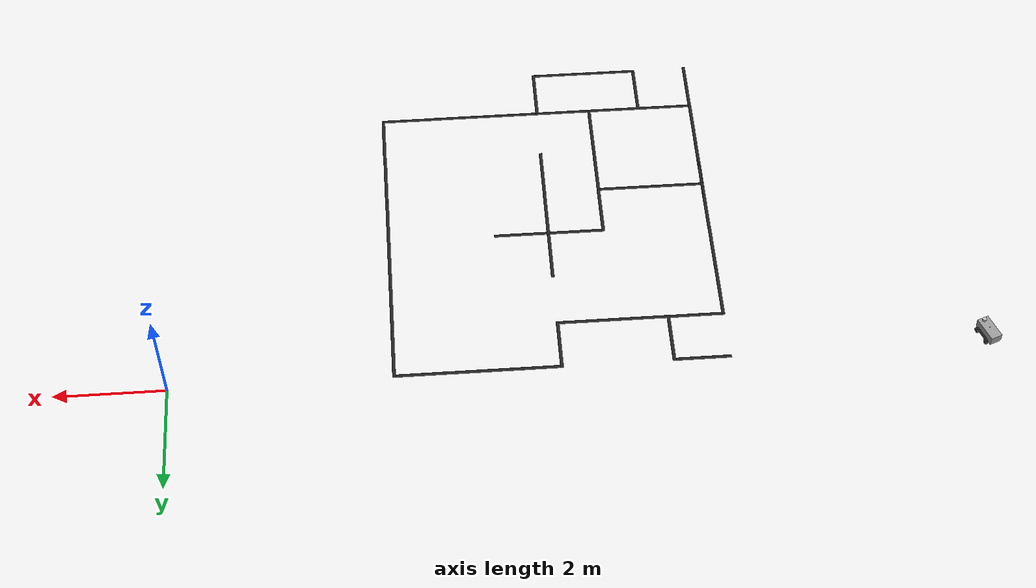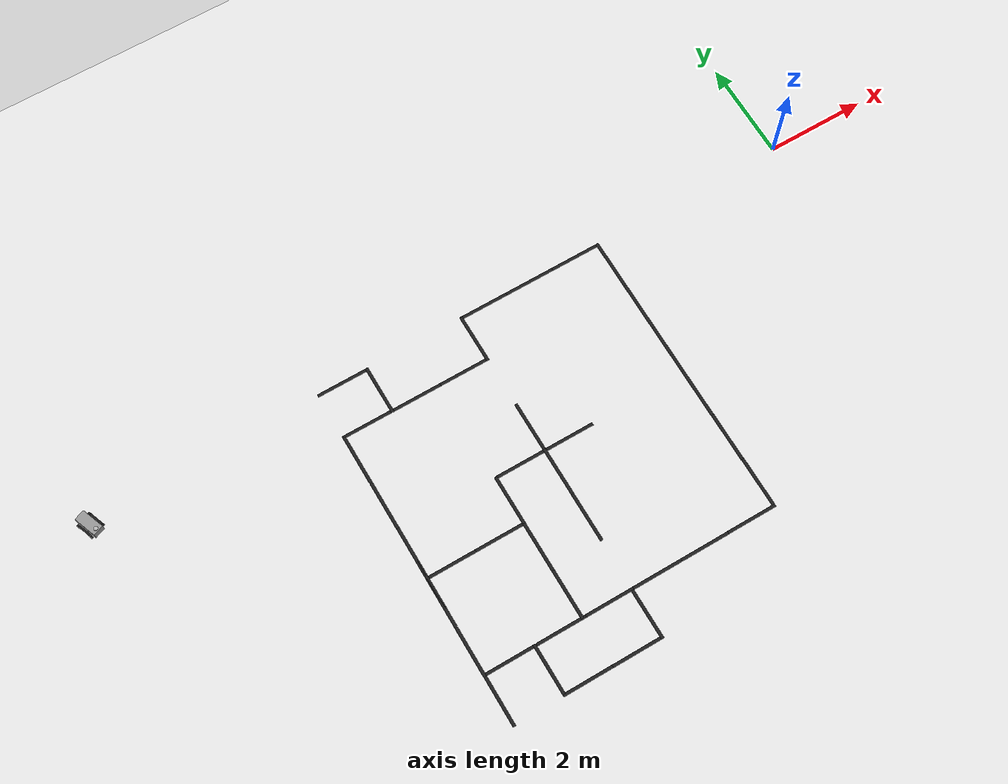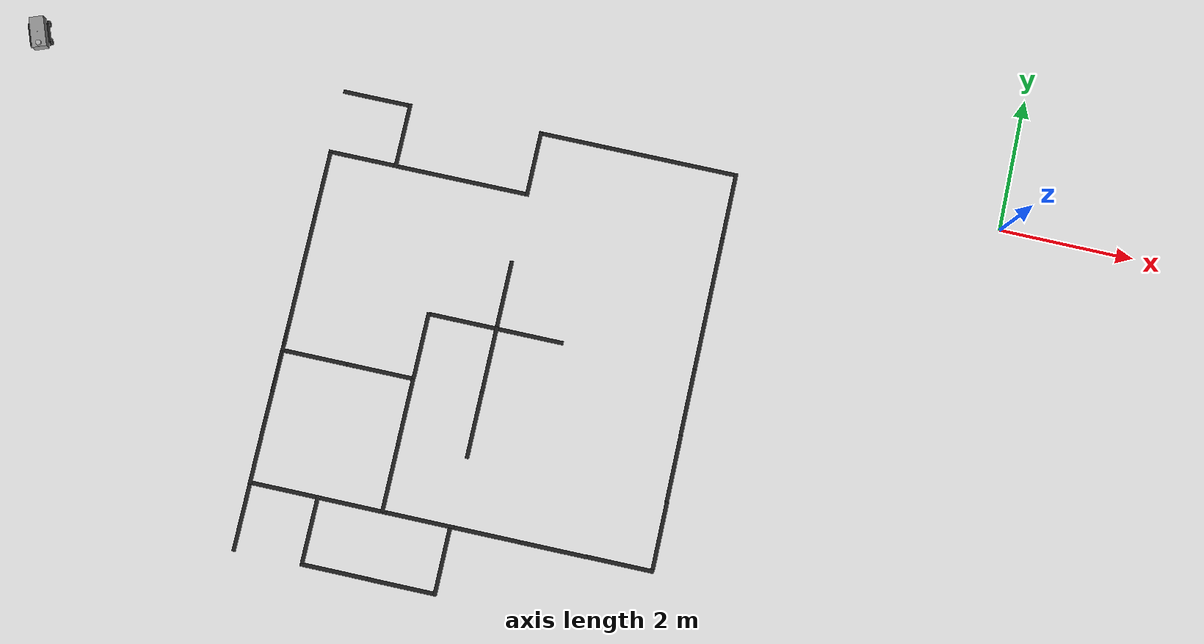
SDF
<sdf version="1.7">
 <world name="default">
  <light name="sun" type="directional">
   <pose>0 0 10 0 -0 0</pose>
   <diffuse>0.8 0.8 0.8 1</diffuse>
   <specular>0.2 0.2 0.2 1</specular>
   <attenuation>
    <range>1000</range>
    <constant>0.9</constant>
    <linear>0.01</linear>
    <quadratic>0.001</quadratic>
   </attenuation>
   <direction>-0.5 0.1 -0.9</direction>
   <spot><inner_angle>0</inner_angle><outer_angle>0</outer_angle><falloff>0</falloff></spot>
  </light>
  <model name="ground_plane">
   <static>1</static>
   <link name="link">
    <collision name="collision">
     <geometry><plane><normal>0 0 1</normal><size>100 100</size></plane></geometry>
     <surface>
      <contact><collide_bitmask>65535</collide_bitmask></contact>
      <friction><ode><mu>100</mu><mu2>50</mu2></ode></friction>
     </surface>
    </collision>
    <visual name="visual">
     <cast_shadows>0</cast_shadows>
     <geometry><plane><normal>0 0 1</normal><size>100 100</size></plane></geometry>
     <material>
      <script><uri>file://media/materials/scripts/gazebo.material</uri><name>Gazebo/White</name></script>
     </material>
    </visual>
   </link>
  </model>
  <model name="mbot">
   <pose>-14.6225 -0.161917 0 4e-06 2e-05 -1.20225</pose>
   <frame name="tankbot::__model__" attached_to="tankbot::chassis">
    <pose relative_to="__model__">0 0 0 0 -0 0</pose>
   </frame>
   <link name="tankbot::chassis">
    <pose relative_to="tankbot::__model__">0 0 0.135 0 -0 0</pose>
    <inertial>
     <pose>0.0465 0 0 0 -0 0</pose>
     <mass>2</mass>
     <inertia>
      <ixx>0.0125927</ixx>
      <iyy>0.0408542</iyy>
      <izz>0.0438135</izz>
      <ixy>0</ixy>
      <ixz>0</ixz>
      <iyz>0</iyz>
     </inertia>
    </inertial>
    <collision name="collision"><geometry><box><size>0.465 0.216 0.17</size></box></geometry></collision>
    <visual name="visual">
     <geometry><box><size>0.465 0.216 0.17</size></box></geometry>
     <material>
      <script><uri>file://media/materials/scripts/gazebo.material</uri><name>Gazebo/Grey</name></script>
     </material>
    </visual>
   </link>
   <link name="tankbot::wheel_fl">
    <pose relative_to="tankbot::__model__">0.1395 0.142 0.05 -1.5708 -0.087266 0</pose>
    <inertial>
     <mass>0.25</mass>
     <inertia>
      <ixx>0.000189583</ixx>
      <iyy>0.000189583</iyy>
      <izz>0.0003125</izz>
      <ixy>0</ixy>
      <ixz>0</ixz>
      <iyz>0</iyz>
     </inertia>
    </inertial>
    <collision name="collision">
     <geometry><cylinder><radius>0.05</radius><length>0.04</length></cylinder></geometry>
    </collision>
    <visual name="tankbot::wheel_fl">
     <geometry><cylinder><radius>0.05</radius><length>0.04</length></cylinder></geometry>
     <material>
      <script><uri>file://media/materials/scripts/gazebo.material</uri><name>Gazebo/Black</name></script>
     </material>
    </visual>
   </link>
   <joint name="tankbot::wheel_fl_drive" type="revolute">
    <parent>tankbot::chassis</parent>
    <child>tankbot::wheel_fl</child>
    <axis>
     <xyz>0 0 1</xyz>
     <limit><lower>-1e+16</lower><upper>1e+16</upper></limit>
     <dynamics><spring_reference>0</spring_reference><spring_stiffness>0</spring_stiffness></dynamics>
    </axis>
   </joint>
   <link name="tankbot::chain_l_up">
    <pose relative_to="tankbot::__model__">0.0098 0.14 0.1 0 -0 0</pose>
    <gravity>0</gravity>
    <collision name="collision"><geometry><box><size>0.28 0.04 0.01</size></box></geometry></collision>
    <visual name="visual">
     <geometry><box><size>0.28 0.04 0.01</size></box></geometry>
     <material>
      <script><uri>file://media/materials/scripts/gazebo.material</uri><name>Gazebo/Black</name></script>
     </material>
    </visual>
    <inertial>
     <inertia><ixx>1</ixx><ixy>0</ixy><ixz>0</ixz><iyy>1</iyy><iyz>0</iyz><izz>1</izz></inertia>
     <mass>1</mass>
    </inertial>
   </link>
   <link name="tankbot::chain_r_up">
    <pose relative_to="tankbot::__model__">0.0098 -0.14 0.1 0 -0 0</pose>
    <gravity>0</gravity>
    <collision name="collision"><geometry><box><size>0.28 0.04 0.01</size></box></geometry></collision>
    <visual name="visual">
     <geometry><box><size>0.28 0.04 0.01</size></box></geometry>
     <material>
      <script><uri>file://media/materials/scripts/gazebo.material</uri><name>Gazebo/Black</name></script>
     </material>
    </visual>
    <inertial>
     <inertia><ixx>1</ixx><ixy>0</ixy><ixz>0</ixz><iyy>1</iyy><iyz>0</iyz><izz>1</izz></inertia>
     <mass>1</mass>
    </inertial>
   </link>
   <joint name="tankbot::chain_up_joint" type="revolute">
    <parent>tankbot::chassis</parent>
    <child>tankbot::chain_r_up</child>
   </joint>
   <joint name="tankbot::chain_up_2_joint" type="revolute">
    <parent>tankbot::chassis</parent>
    <child>tankbot::chain_l_up</child>
   </joint>
   <link name="tankbot::wheel_fr">
    <pose relative_to="tankbot::__model__">0.1395 -0.142 0.05 -1.5708 -0.087266 0</pose>
    <inertial>
     <mass>0.25</mass>
     <inertia>
      <ixx>0.000189583</ixx>
      <iyy>0.000189583</iyy>
      <izz>0.0003125</izz>
      <ixy>0</ixy>
      <ixz>0</ixz>
      <iyz>0</iyz>
     </inertia>
    </inertial>
    <collision name="collision">
     <geometry><cylinder><radius>0.05</radius><length>0.04</length></cylinder></geometry>
    </collision>
    <visual name="visual">
     <geometry><cylinder><radius>0.05</radius><length>0.04</length></cylinder></geometry>
     <material>
      <script><uri>file://media/materials/scripts/gazebo.material</uri><name>Gazebo/Black</name></script>
     </material>
    </visual>
   </link>
   <joint name="tankbot::wheel_fr_drive" type="revolute">
    <parent>tankbot::chassis</parent>
    <child>tankbot::wheel_fr</child>
    <axis>
     <xyz>0 0 1</xyz>
     <limit><lower>-1e+16</lower><upper>1e+16</upper></limit>
     <dynamics><spring_reference>0</spring_reference><spring_stiffness>0</spring_stiffness></dynamics>
    </axis>
   </joint>
   <link name="tankbot::wheel_rl">
    <pose relative_to="tankbot::__model__">-0.1395 0.142 0.05 -1.5708 0 0</pose>
    <inertial>
     <mass>0.25</mass>
     <inertia>
      <ixx>0.000189583</ixx>
      <iyy>0.000189583</iyy>
      <izz>0.0003125</izz>
      <ixy>0</ixy>
      <ixz>0</ixz>
      <iyz>0</iyz>
     </inertia>
    </inertial>
    <collision name="collision">
     <geometry><cylinder><radius>0.05</radius><length>0.04</length></cylinder></geometry>
    </collision>
    <visual name="visual">
     <geometry><cylinder><radius>0.05</radius><length>0.04</length></cylinder></geometry>
     <material>
      <script><uri>file://media/materials/scripts/gazebo.material</uri><name>Gazebo/Black</name></script>
     </material>
    </visual>
   </link>
   <joint name="tankbot::wheel_rl_drive" type="revolute">
    <parent>tankbot::chassis</parent>
    <child>tankbot::wheel_rl</child>
    <axis>
     <xyz>0 0 1</xyz>
     <limit><lower>-1e+16</lower><upper>1e+16</upper></limit>
     <dynamics><spring_reference>0</spring_reference><spring_stiffness>0</spring_stiffness></dynamics>
    </axis>
   </joint>
   <link name="tankbot::wheel_rr">
    <pose relative_to="tankbot::__model__">-0.1395 -0.142 0.05 -1.5708 0 0</pose>
    <inertial>
     <mass>0.25</mass>
     <inertia>
      <ixx>0.000189583</ixx>
      <iyy>0.000189583</iyy>
      <izz>0.0003125</izz>
      <ixy>0</ixy>
      <ixz>0</ixz>
      <iyz>0</iyz>
     </inertia>
    </inertial>
    <collision name="collision">
     <geometry><cylinder><radius>0.05</radius><length>0.04</length></cylinder></geometry>
    </collision>
    <visual name="visual">
     <geometry><cylinder><radius>0.05</radius><length>0.04</length></cylinder></geometry>
     <material>
      <script><uri>file://media/materials/scripts/gazebo.material</uri><name>Gazebo/Black</name></script>
     </material>
    </visual>
   </link>
   <joint name="tankbot::wheel_rr_drive" type="revolute">
    <parent>tankbot::chassis</parent>
    <child>tankbot::wheel_rr</child>
    <axis>
     <xyz>0 0 1</xyz>
     <limit><lower>-1e+16</lower><upper>1e+16</upper></limit>
     <dynamics><spring_reference>0</spring_reference><spring_stiffness>0</spring_stiffness></dynamics>
    </axis>
   </joint>
   <frame name="tankbot::ultrasonic_sensor::__model__" attached_to="tankbot::ultrasonic_sensor::link">
    <pose relative_to="tankbot::__model__">0.18 0 0.24 0 -0 0</pose>
   </frame>
   <link name="tankbot::ultrasonic_sensor::link">
    <inertial>
     <mass>0.1</mass>
     <inertia><ixx>1</ixx><ixy>0</ixy><ixz>0</ixz><iyy>1</iyy><iyz>0</iyz><izz>1</izz></inertia>
    </inertial>
    <visual name="visual">
     <geometry><cylinder><radius>0.04</radius><length>0.04</length></cylinder></geometry>
    </visual>
    <collision name="collision-base">
     <pose>0 0 -0.0145 0 -0 0</pose>
     <geometry><box><size>0.05 0.05 0.041</size></box></geometry>
    </collision>
    <collision name="collision-top">
     <pose>0 0 0.0205 0 -0 0</pose>
     <geometry><cylinder><radius>0.021</radius><length>0.029</length></cylinder></geometry>
    </collision>
    <sensor name="sonar" type="sonar">
     <pose>0.04 0 0 0 1.5 3.14</pose>
     <sonar><min>0</min><max>3</max><radius>0.3</radius></sonar>
     <plugin name="sonar" filename="libSonarPlugin.so"/>
     <always_on>1</always_on>
     <update_rate>30</update_rate>
     <visualize>1</visualize>
    </sensor>
    <pose relative_to="tankbot::ultrasonic_sensor::__model__">0 0 0 0 -0 0</pose>
   </link>
   <joint name="tankbot::sonar_joint" type="fixed">
    <child>tankbot::ultrasonic_sensor::link</child>
    <parent>tankbot::chassis</parent>
   </joint>
   <frame name="tankbot::camera_sensor::__model__" attached_to="tankbot::camera_sensor::link">
    <pose relative_to="tankbot::__model__">0.2 0 0.04 0 1.57 0</pose>
   </frame>
   <frame name="tankbot::camera_sensor_2::__model__" attached_to="tankbot::camera_sensor::link_2">
    <pose relative_to="tankbot::__model__">0.15 -0.07 0.04 0 1.57 0</pose>
   </frame>
   <link name="tankbot::camera_sensor::link">
    <inertial>
     <mass>0.1</mass>
     <inertia><ixx>1</ixx><ixy>0</ixy><ixz>0</ixz><iyy>1</iyy><iyz>0</iyz><izz>1</izz></inertia>
    </inertial>
    <visual name="visual">
     <geometry><box><size>0.01 0.07 0.04</size></box></geometry>
     <material>
      <script><uri>file://media/materials/scripts/gazebo.material</uri><name>Gazebo/Red</name></script>
     </material>
    </visual>
    <collision name="collision">
     <pose>0 0 -0.0145 0 -0 0</pose>
     <geometry><box><size>0.01 0.07 0.04</size></box></geometry>
    </collision>
    <sensor name="camera" type="camera">
     <camera>
      <horizontal_fov>1.39626</horizontal_fov>
      <image><width>2</width><height>2</height></image>
      <clip><near>0.02</near><far>300</far></clip>
     </camera>
     <always_on>1</always_on>
     <update_rate>10</update_rate>
     <visualize>1</visualize>
     <plugin name="camera_controller" filename="libCameraPlugin.so"/>
    </sensor>
    <pose relative_to="tankbot::camera_sensor::__model__">0 0 0 0 -0 0</pose>
   </link>
   <link name="tankbot::camera_sensor::link_2">
    <inertial>
     <mass>0.1</mass>
     <inertia><ixx>1</ixx><ixy>0</ixy><ixz>0</ixz><iyy>1</iyy><iyz>0</iyz><izz>1</izz></inertia>
    </inertial>
    <visual name="visual">
     <geometry><box><size>0.01 0.07 0.04</size></box></geometry>
     <material>
      <script><uri>file://media/materials/scripts/gazebo.material</uri><name>Gazebo/Red</name></script>
     </material>
    </visual>
    <collision name="collision">
     <pose>0 0 -0.0145 0 -0 0</pose>
     <geometry><box><size>0.01 0.07 0.04</size></box></geometry>
    </collision>
    <sensor name="camera" type="camera">
     <camera>
      <horizontal_fov>1.39626</horizontal_fov>
      <image><width>2</width><height>2</height></image>
      <clip><near>0.02</near><far>300</far></clip>
     </camera>
     <always_on>1</always_on>
     <update_rate>10</update_rate>
     <visualize>1</visualize>
     <plugin name="camera_controller" filename="libCameraPlugin.so"/>
    </sensor>
    <pose relative_to="tankbot::camera_sensor_2::__model__">0 0 0 0 -0 0</pose>
   </link>
   <frame name="tankbot::microphone_sensor::__model__" attached_to="tankbot::microphone_sensor::link">
    <pose relative_to="tankbot::__model__">0 0 0.23 0 -0 0</pose>
   </frame>
   <link name="tankbot::microphone_sensor::link">
    <inertial>
     <mass>0.1</mass>
     <inertia><ixx>1</ixx><ixy>0</ixy><ixz>0</ixz><iyy>1</iyy><iyz>0</iyz><izz>1</izz></inertia>
    </inertial>
    <visual name="visual">
     <geometry><box><size>0.01 0.01 0.01</size></box></geometry>
     <material>
      <script><uri>file://media/materials/scripts/gazebo.material</uri><name>Gazebo/Grey</name></script>
     </material>
    </visual>
    <collision name="collision"><geometry><box><size>0.01 0.01 0.01</size></box></geometry></collision>
    <pose relative_to="tankbot::microphone_sensor::__model__">0 0 0 0 -0 0</pose>
   </link>
   <plugin name="microphone_controller" filename="libmicrophone_control_plugin.so"/>
   <joint name="tankbot::camera_joint" type="fixed">
    <child>tankbot::camera_sensor::link</child>
    <parent>tankbot::chassis</parent>
   </joint>
   <joint name="tankbot::camera_joint_2" type="fixed">
    <child>tankbot::camera_sensor::link_2</child>
    <parent>tankbot::chassis</parent>
   </joint>
   <plugin name="tankbot_control" filename="libtank_control_plugin.so"/>
  </model>
  <gravity>0 0 -9.8</gravity>
  <magnetic_field>6e-06 2.3e-05 -4.2e-05</magnetic_field>
  <atmosphere type="adiabatic"/>
  <physics type="ode">
   <max_step_size>0.001</max_step_size>
   <real_time_factor>1</real_time_factor>
   <real_time_update_rate>1000</real_time_update_rate>
  </physics>
  <scene><ambient>0.4 0.4 0.4 1</ambient><background>0.7 0.7 0.7 1</background><shadows>1</shadows></scene>
  <spherical_coordinates>
   <surface_model>EARTH_WGS84</surface_model>
   <latitude_deg>0</latitude_deg>
   <longitude_deg>0</longitude_deg>
   <elevation>0</elevation>
   <heading_deg>0</heading_deg>
  </spherical_coordinates>
  <model name="right_segment">
   <link name="right_link">
    <inertial>
     <mass>1</mass>
     <inertia>
      <ixx>0.166667</ixx>
      <ixy>0</ixy>
      <ixz>0</ixz>
      <iyy>0.166667</iyy>
      <iyz>0</iyz>
      <izz>0.166667</izz>
     </inertia>
    </inertial>
    <visual name="visual">
     <geometry><box><size>0.06 1 0.000937</size></box></geometry>
     <material>
      <script><name>Gazebo/Black</name><uri>file://media/materials/scripts/gazebo.material</uri></script>
      <shader type="pixel"><normal_map>__default__</normal_map></shader>
      <ambient>0 0 0 1</ambient>
      <diffuse>0 0 0 1</diffuse>
      <specular>0.1 0.1 0.1 1</specular>
      <emissive>0 0 0 1</emissive>
     </material>
    </visual>
    <collision name="collision">
     <geometry><box><size>0.06 1 0.000937</size></box></geometry>
     <surface>
      <friction>
       <ode><mu>1</mu><mu2>1</mu2><fdir1>0 0 0</fdir1><slip1>0</slip1><slip2>0</slip2></ode>
       <torsional>
        <coefficient>1</coefficient>
        <patch_radius>0</patch_radius>
        <surface_radius>0</surface_radius>
        <use_patch_radius>1</use_patch_radius>
        <ode><slip>0</slip></ode>
       </torsional>
      </friction>
      <bounce><restitution_coefficient>0</restitution_coefficient><threshold>1e+06</threshold></bounce>
      <contact>
       <collide_without_contact>0</collide_without_contact>
       <collide_without_contact_bitmask>1</collide_without_contact_bitmask>
       <collide_bitmask>1</collide_bitmask>
       <ode>
        <soft_cfm>0</soft_cfm>
        <soft_erp>0.2</soft_erp>
        <kp>1e+13</kp>
        <kd>1</kd>
        <max_vel>0.01</max_vel>
        <min_depth>0</min_depth>
       </ode>
       <bullet>
        <split_impulse>1</split_impulse>
        <split_impulse_penetration_threshold>-0.01</split_impulse_penetration_threshold>
        <soft_cfm>0</soft_cfm>
        <soft_erp>0.2</soft_erp>
        <kp>1e+13</kp>
        <kd>1</kd>
       </bullet>
      </contact>
     </surface>
    </collision>
   </link>
   <static>1</static>
   <pose>-8.96406 -0.498196 0.000468 0 -0 1.4e-05</pose>
  </model>
  <model name="segment_0">
   <link name="straight_link">
    <inertial>
     <mass>1</mass>
     <inertia>
      <ixx>0.166667</ixx>
      <ixy>0</ixy>
      <ixz>0</ixz>
      <iyy>0.166667</iyy>
      <iyz>0</iyz>
      <izz>0.166667</izz>
     </inertia>
    </inertial>
    <visual name="visual">
     <geometry><box><size>1 0.06 0.000937</size></box></geometry>
     <material>
      <script><name>Gazebo/Black</name><uri>file://media/materials/scripts/gazebo.material</uri></script>
      <shader type="pixel"><normal_map>__default__</normal_map></shader>
      <ambient>0 0 0 1</ambient>
      <diffuse>0 0 0 1</diffuse>
      <specular>0.1 0.1 0.1 1</specular>
      <emissive>0 0 0 1</emissive>
     </material>
    </visual>
    <collision name="collision">
     <geometry><box><size>1 0.06 0.000937</size></box></geometry>
     <surface>
      <friction>
       <ode><mu>1</mu><mu2>1</mu2><fdir1>0 0 0</fdir1><slip1>0</slip1><slip2>0</slip2></ode>
       <torsional>
        <coefficient>1</coefficient>
        <patch_radius>0</patch_radius>
        <surface_radius>0</surface_radius>
        <use_patch_radius>1</use_patch_radius>
        <ode><slip>0</slip></ode>
       </torsional>
      </friction>
      <bounce><restitution_coefficient>0</restitution_coefficient><threshold>1e+06</threshold></bounce>
      <contact>
       <collide_without_contact>0</collide_without_contact>
       <collide_without_contact_bitmask>1</collide_without_contact_bitmask>
       <collide_bitmask>1</collide_bitmask>
       <ode>
        <soft_cfm>0</soft_cfm>
        <soft_erp>0.2</soft_erp>
        <kp>1e+13</kp>
        <kd>1</kd>
        <max_vel>0.01</max_vel>
        <min_depth>0</min_depth>
       </ode>
       <bullet>
        <split_impulse>1</split_impulse>
        <split_impulse_penetration_threshold>-0.01</split_impulse_penetration_threshold>
        <soft_cfm>0</soft_cfm>
        <soft_erp>0.2</soft_erp>
        <kp>1e+13</kp>
        <kd>1</kd>
       </bullet>
      </contact>
     </surface>
    </collision>
   </link>
   <static>1</static>
   <pose>-9.49128 -0.967715 0 0 -0 0</pose>
  </model>
  <model name="segment_1">
   <link name="straight_link">
    <inertial>
     <mass>1</mass>
     <inertia>
      <ixx>0.166667</ixx>
      <ixy>0</ixy>
      <ixz>0</ixz>
      <iyy>0.166667</iyy>
      <iyz>0</iyz>
      <izz>0.166667</izz>
     </inertia>
    </inertial>
    <visual name="visual">
     <geometry><box><size>1 0.06 0.000937</size></box></geometry>
     <material>
      <script><name>Gazebo/Black</name><uri>file://media/materials/scripts/gazebo.material</uri></script>
      <shader type="pixel"><normal_map>__default__</normal_map></shader>
      <ambient>0 0 0 1</ambient>
      <diffuse>0 0 0 1</diffuse>
      <specular>0.1 0.1 0.1 1</specular>
      <emissive>0 0 0 1</emissive>
     </material>
    </visual>
    <collision name="collision">
     <geometry><box><size>1 0.06 0.000937</size></box></geometry>
     <surface>
      <friction>
       <ode><mu>1</mu><mu2>1</mu2><fdir1>0 0 0</fdir1><slip1>0</slip1><slip2>0</slip2></ode>
       <torsional>
        <coefficient>1</coefficient>
        <patch_radius>0</patch_radius>
        <surface_radius>0</surface_radius>
        <use_patch_radius>1</use_patch_radius>
        <ode><slip>0</slip></ode>
       </torsional>
      </friction>
      <bounce><restitution_coefficient>0</restitution_coefficient><threshold>1e+06</threshold></bounce>
      <contact>
       <collide_without_contact>0</collide_without_contact>
       <collide_without_contact_bitmask>1</collide_without_contact_bitmask>
       <collide_bitmask>1</collide_bitmask>
       <ode>
        <soft_cfm>0</soft_cfm>
        <soft_erp>0.2</soft_erp>
        <kp>1e+13</kp>
        <kd>1</kd>
        <max_vel>0.01</max_vel>
        <min_depth>0</min_depth>
       </ode>
       <bullet>
        <split_impulse>1</split_impulse>
        <split_impulse_penetration_threshold>-0.01</split_impulse_penetration_threshold>
        <soft_cfm>0</soft_cfm>
        <soft_erp>0.2</soft_erp>
        <kp>1e+13</kp>
        <kd>1</kd>
       </bullet>
      </contact>
     </surface>
    </collision>
   </link>
   <static>1</static>
   <pose>-8.45229 -0.969593 0 0 -0 0</pose>
  </model>
  <model name="segment">
   <link name="straight_link">
    <inertial>
     <mass>1</mass>
     <inertia>
      <ixx>0.166667</ixx>
      <ixy>0</ixy>
      <ixz>0</ixz>
      <iyy>0.166667</iyy>
      <iyz>0</iyz>
      <izz>0.166667</izz>
     </inertia>
    </inertial>
    <visual name="visual">
     <geometry><box><size>1 0.06 0.000937</size></box></geometry>
     <material>
      <script><name>Gazebo/Black</name><uri>file://media/materials/scripts/gazebo.material</uri></script>
      <shader type="pixel"><normal_map>__default__</normal_map></shader>
      <ambient>0 0 0 1</ambient>
      <diffuse>0 0 0 1</diffuse>
      <specular>0.1 0.1 0.1 1</specular>
      <emissive>0 0 0 1</emissive>
     </material>
    </visual>
    <collision name="collision">
     <geometry><box><size>1 0.06 0.000937</size></box></geometry>
     <surface>
      <friction>
       <ode><mu>1</mu><mu2>1</mu2><fdir1>0 0 0</fdir1><slip1>0</slip1><slip2>0</slip2></ode>
       <torsional>
        <coefficient>1</coefficient>
        <patch_radius>0</patch_radius>
        <surface_radius>0</surface_radius>
        <use_patch_radius>1</use_patch_radius>
        <ode><slip>0</slip></ode>
       </torsional>
      </friction>
      <bounce><restitution_coefficient>0</restitution_coefficient><threshold>1e+06</threshold></bounce>
      <contact>
       <collide_without_contact>0</collide_without_contact>
       <collide_without_contact_bitmask>1</collide_without_contact_bitmask>
       <collide_bitmask>1</collide_bitmask>
       <ode>
        <soft_cfm>0</soft_cfm>
        <soft_erp>0.2</soft_erp>
        <kp>1e+13</kp>
        <kd>1</kd>
        <max_vel>0.01</max_vel>
        <min_depth>0</min_depth>
       </ode>
       <bullet>
        <split_impulse>1</split_impulse>
        <split_impulse_penetration_threshold>-0.01</split_impulse_penetration_threshold>
        <soft_cfm>0</soft_cfm>
        <soft_erp>0.2</soft_erp>
        <kp>1e+13</kp>
        <kd>1</kd>
       </bullet>
      </contact>
     </surface>
    </collision>
   </link>
   <static>1</static>
   <pose>-9.49006 -0.029184 0 0 -0 0</pose>
  </model>
  <model name="right_segment_1">
   <link name="right_link">
    <inertial>
     <mass>1</mass>
     <inertia>
      <ixx>0.166667</ixx>
      <ixy>0</ixy>
      <ixz>0</ixz>
      <iyy>0.166667</iyy>
      <iyz>0</iyz>
      <izz>0.166667</izz>
     </inertia>
    </inertial>
    <visual name="visual">
     <geometry><box><size>0.06 1 0.000937</size></box></geometry>
     <material>
      <script><name>Gazebo/Black</name><uri>file://media/materials/scripts/gazebo.material</uri></script>
      <shader type="pixel"><normal_map>__default__</normal_map></shader>
      <ambient>0 0 0 1</ambient>
      <diffuse>0 0 0 1</diffuse>
      <specular>0.1 0.1 0.1 1</specular>
      <emissive>0 0 0 1</emissive>
     </material>
    </visual>
    <collision name="collision">
     <geometry><box><size>0.06 1 0.000937</size></box></geometry>
     <surface>
      <friction>
       <ode><mu>1</mu><mu2>1</mu2><fdir1>0 0 0</fdir1><slip1>0</slip1><slip2>0</slip2></ode>
       <torsional>
        <coefficient>1</coefficient>
        <patch_radius>0</patch_radius>
        <surface_radius>0</surface_radius>
        <use_patch_radius>1</use_patch_radius>
        <ode><slip>0</slip></ode>
       </torsional>
      </friction>
      <bounce><restitution_coefficient>0</restitution_coefficient><threshold>1e+06</threshold></bounce>
      <contact>
       <collide_without_contact>0</collide_without_contact>
       <collide_without_contact_bitmask>1</collide_without_contact_bitmask>
       <collide_bitmask>1</collide_bitmask>
       <ode>
        <soft_cfm>0</soft_cfm>
        <soft_erp>0.2</soft_erp>
        <kp>1e+13</kp>
        <kd>1</kd>
        <max_vel>0.01</max_vel>
        <min_depth>0</min_depth>
       </ode>
       <bullet>
        <split_impulse>1</split_impulse>
        <split_impulse_penetration_threshold>-0.01</split_impulse_penetration_threshold>
        <soft_cfm>0</soft_cfm>
        <soft_erp>0.2</soft_erp>
        <kp>1e+13</kp>
        <kd>1</kd>
       </bullet>
      </contact>
     </surface>
    </collision>
   </link>
   <static>1</static>
   <pose>-6.96035 -0.49852 0.000468 0 -0 1.4e-05</pose>
  </model>
  <model name="right_segment_3">
   <link name="right_link">
    <inertial>
     <mass>1</mass>
     <inertia>
      <ixx>0.166667</ixx>
      <ixy>0</ixy>
      <ixz>0</ixz>
      <iyy>0.166667</iyy>
      <iyz>0</iyz>
      <izz>0.166667</izz>
     </inertia>
    </inertial>
    <visual name="visual">
     <geometry><box><size>0.06 1 0.000937</size></box></geometry>
     <material>
      <script><name>Gazebo/Black</name><uri>file://media/materials/scripts/gazebo.material</uri></script>
      <shader type="pixel"><normal_map>__default__</normal_map></shader>
      <ambient>0 0 0 1</ambient>
      <diffuse>0 0 0 1</diffuse>
      <specular>0.1 0.1 0.1 1</specular>
      <emissive>0 0 0 1</emissive>
     </material>
    </visual>
    <collision name="collision">
     <geometry><box><size>0.06 1 0.000937</size></box></geometry>
     <surface>
      <friction>
       <ode><mu>1</mu><mu2>1</mu2><fdir1>0 0 0</fdir1><slip1>0</slip1><slip2>0</slip2></ode>
       <torsional>
        <coefficient>1</coefficient>
        <patch_radius>0</patch_radius>
        <surface_radius>0</surface_radius>
        <use_patch_radius>1</use_patch_radius>
        <ode><slip>0</slip></ode>
       </torsional>
      </friction>
      <bounce><restitution_coefficient>0</restitution_coefficient><threshold>1e+06</threshold></bounce>
      <contact>
       <collide_without_contact>0</collide_without_contact>
       <collide_without_contact_bitmask>1</collide_without_contact_bitmask>
       <collide_bitmask>1</collide_bitmask>
       <ode>
        <soft_cfm>0</soft_cfm>
        <soft_erp>0.2</soft_erp>
        <kp>1e+13</kp>
        <kd>1</kd>
        <max_vel>0.01</max_vel>
        <min_depth>0</min_depth>
       </ode>
       <bullet>
        <split_impulse>1</split_impulse>
        <split_impulse_penetration_threshold>-0.01</split_impulse_penetration_threshold>
        <soft_cfm>0</soft_cfm>
        <soft_erp>0.2</soft_erp>
        <kp>1e+13</kp>
        <kd>1</kd>
       </bullet>
      </contact>
     </surface>
    </collision>
   </link>
   <static>1</static>
   <pose>-6.95925 -2.49328 0.000468 0 -0 1.4e-05</pose>
  </model>
  <model name="right_segment_4">
   <link name="right_link">
    <inertial>
     <mass>1</mass>
     <inertia>
      <ixx>0.166667</ixx>
      <ixy>0</ixy>
      <ixz>0</ixz>
      <iyy>0.166667</iyy>
      <iyz>0</iyz>
      <izz>0.166667</izz>
     </inertia>
    </inertial>
    <visual name="visual">
     <geometry><box><size>0.06 1 0.000937</size></box></geometry>
     <material>
      <script><name>Gazebo/Black</name><uri>file://media/materials/scripts/gazebo.material</uri></script>
      <shader type="pixel"><normal_map>__default__</normal_map></shader>
      <ambient>0 0 0 1</ambient>
      <diffuse>0 0 0 1</diffuse>
      <specular>0.1 0.1 0.1 1</specular>
      <emissive>0 0 0 1</emissive>
     </material>
    </visual>
    <collision name="collision">
     <geometry><box><size>0.06 1 0.000937</size></box></geometry>
     <surface>
      <friction>
       <ode><mu>1</mu><mu2>1</mu2><fdir1>0 0 0</fdir1><slip1>0</slip1><slip2>0</slip2></ode>
       <torsional>
        <coefficient>1</coefficient>
        <patch_radius>0</patch_radius>
        <surface_radius>0</surface_radius>
        <use_patch_radius>1</use_patch_radius>
        <ode><slip>0</slip></ode>
       </torsional>
      </friction>
      <bounce><restitution_coefficient>0</restitution_coefficient><threshold>1e+06</threshold></bounce>
      <contact>
       <collide_without_contact>0</collide_without_contact>
       <collide_without_contact_bitmask>1</collide_without_contact_bitmask>
       <collide_bitmask>1</collide_bitmask>
       <ode>
        <soft_cfm>0</soft_cfm>
        <soft_erp>0.2</soft_erp>
        <kp>1e+13</kp>
        <kd>1</kd>
        <max_vel>0.01</max_vel>
        <min_depth>0</min_depth>
       </ode>
       <bullet>
        <split_impulse>1</split_impulse>
        <split_impulse_penetration_threshold>-0.01</split_impulse_penetration_threshold>
        <soft_cfm>0</soft_cfm>
        <soft_erp>0.2</soft_erp>
        <kp>1e+13</kp>
        <kd>1</kd>
       </bullet>
      </contact>
     </surface>
    </collision>
   </link>
   <static>1</static>
   <pose>-6.95916 -3.47904 0.000468 0 -0 1.4e-05</pose>
  </model>
  <model name="right_segment_5">
   <link name="right_link">
    <inertial>
     <mass>1</mass>
     <inertia>
      <ixx>0.166667</ixx>
      <ixy>0</ixy>
      <ixz>0</ixz>
      <iyy>0.166667</iyy>
      <iyz>0</iyz>
      <izz>0.166667</izz>
     </inertia>
    </inertial>
    <visual name="visual">
     <geometry><box><size>0.06 1 0.000937</size></box></geometry>
     <material>
      <script><name>Gazebo/Black</name><uri>file://media/materials/scripts/gazebo.material</uri></script>
      <shader type="pixel"><normal_map>__default__</normal_map></shader>
      <ambient>0 0 0 1</ambient>
      <diffuse>0 0 0 1</diffuse>
      <specular>0.1 0.1 0.1 1</specular>
      <emissive>0 0 0 1</emissive>
     </material>
    </visual>
    <collision name="collision">
     <geometry><box><size>0.06 1 0.000937</size></box></geometry>
     <surface>
      <friction>
       <ode><mu>1</mu><mu2>1</mu2><fdir1>0 0 0</fdir1><slip1>0</slip1><slip2>0</slip2></ode>
       <torsional>
        <coefficient>1</coefficient>
        <patch_radius>0</patch_radius>
        <surface_radius>0</surface_radius>
        <use_patch_radius>1</use_patch_radius>
        <ode><slip>0</slip></ode>
       </torsional>
      </friction>
      <bounce><restitution_coefficient>0</restitution_coefficient><threshold>1e+06</threshold></bounce>
      <contact>
       <collide_without_contact>0</collide_without_contact>
       <collide_without_contact_bitmask>1</collide_without_contact_bitmask>
       <collide_bitmask>1</collide_bitmask>
       <ode>
        <soft_cfm>0</soft_cfm>
        <soft_erp>0.2</soft_erp>
        <kp>1e+13</kp>
        <kd>1</kd>
        <max_vel>0.01</max_vel>
        <min_depth>0</min_depth>
       </ode>
       <bullet>
        <split_impulse>1</split_impulse>
        <split_impulse_penetration_threshold>-0.01</split_impulse_penetration_threshold>
        <soft_cfm>0</soft_cfm>
        <soft_erp>0.2</soft_erp>
        <kp>1e+13</kp>
        <kd>1</kd>
       </bullet>
      </contact>
     </surface>
    </collision>
   </link>
   <static>1</static>
   <pose>-6.96112 -4.47675 0.000468 0 -0 1.4e-05</pose>
  </model>
  <model name="segment_3">
   <link name="straight_link">
    <inertial>
     <mass>1</mass>
     <inertia>
      <ixx>0.166667</ixx>
      <ixy>0</ixy>
      <ixz>0</ixz>
      <iyy>0.166667</iyy>
      <iyz>0</iyz>
      <izz>0.166667</izz>
     </inertia>
    </inertial>
    <visual name="visual">
     <geometry><box><size>1 0.06 0.000937</size></box></geometry>
     <material>
      <script><name>Gazebo/Black</name><uri>file://media/materials/scripts/gazebo.material</uri></script>
      <shader type="pixel"><normal_map>__default__</normal_map></shader>
      <ambient>0 0 0 1</ambient>
      <diffuse>0 0 0 1</diffuse>
      <specular>0.1 0.1 0.1 1</specular>
      <emissive>0 0 0 1</emissive>
     </material>
    </visual>
    <collision name="collision">
     <geometry><box><size>1 0.06 0.000937</size></box></geometry>
     <surface>
      <friction>
       <ode><mu>1</mu><mu2>1</mu2><fdir1>0 0 0</fdir1><slip1>0</slip1><slip2>0</slip2></ode>
       <torsional>
        <coefficient>1</coefficient>
        <patch_radius>0</patch_radius>
        <surface_radius>0</surface_radius>
        <use_patch_radius>1</use_patch_radius>
        <ode><slip>0</slip></ode>
       </torsional>
      </friction>
      <bounce><restitution_coefficient>0</restitution_coefficient><threshold>1e+06</threshold></bounce>
      <contact>
       <collide_without_contact>0</collide_without_contact>
       <collide_without_contact_bitmask>1</collide_without_contact_bitmask>
       <collide_bitmask>1</collide_bitmask>
       <ode>
        <soft_cfm>0</soft_cfm>
        <soft_erp>0.2</soft_erp>
        <kp>1e+13</kp>
        <kd>1</kd>
        <max_vel>0.01</max_vel>
        <min_depth>0</min_depth>
       </ode>
       <bullet>
        <split_impulse>1</split_impulse>
        <split_impulse_penetration_threshold>-0.01</split_impulse_penetration_threshold>
        <soft_cfm>0</soft_cfm>
        <soft_erp>0.2</soft_erp>
        <kp>1e+13</kp>
        <kd>1</kd>
       </bullet>
      </contact>
     </surface>
    </collision>
   </link>
   <static>1</static>
   <pose>-7.4559 -0.969503 0 0 -0 0</pose>
  </model>
  <model name="segment_2">
   <link name="straight_link">
    <inertial>
     <mass>1</mass>
     <inertia>
      <ixx>0.166667</ixx>
      <ixy>0</ixy>
      <ixz>0</ixz>
      <iyy>0.166667</iyy>
      <iyz>0</iyz>
      <izz>0.166667</izz>
     </inertia>
    </inertial>
    <visual name="visual">
     <geometry><box><size>1 0.06 0.000937</size></box></geometry>
     <material>
      <script><name>Gazebo/Black</name><uri>file://media/materials/scripts/gazebo.material</uri></script>
      <shader type="pixel"><normal_map>__default__</normal_map></shader>
      <ambient>0 0 0 1</ambient>
      <diffuse>0 0 0 1</diffuse>
      <specular>0.1 0.1 0.1 1</specular>
      <emissive>0 0 0 1</emissive>
     </material>
    </visual>
    <collision name="collision">
     <geometry><box><size>1 0.06 0.000937</size></box></geometry>
     <surface>
      <friction>
       <ode><mu>1</mu><mu2>1</mu2><fdir1>0 0 0</fdir1><slip1>0</slip1><slip2>0</slip2></ode>
       <torsional>
        <coefficient>1</coefficient>
        <patch_radius>0</patch_radius>
        <surface_radius>0</surface_radius>
        <use_patch_radius>1</use_patch_radius>
        <ode><slip>0</slip></ode>
       </torsional>
      </friction>
      <bounce><restitution_coefficient>0</restitution_coefficient><threshold>1e+06</threshold></bounce>
      <contact>
       <collide_without_contact>0</collide_without_contact>
       <collide_without_contact_bitmask>1</collide_without_contact_bitmask>
       <collide_bitmask>1</collide_bitmask>
       <ode>
        <soft_cfm>0</soft_cfm>
        <soft_erp>0.2</soft_erp>
        <kp>1e+13</kp>
        <kd>1</kd>
        <max_vel>0.01</max_vel>
        <min_depth>0</min_depth>
       </ode>
       <bullet>
        <split_impulse>1</split_impulse>
        <split_impulse_penetration_threshold>-0.01</split_impulse_penetration_threshold>
        <soft_cfm>0</soft_cfm>
        <soft_erp>0.2</soft_erp>
        <kp>1e+13</kp>
        <kd>1</kd>
       </bullet>
      </contact>
     </surface>
    </collision>
   </link>
   <static>1</static>
   <pose>-6.4877 -0.020685 0 0 -0 0</pose>
  </model>
  <model name="segment_4">
   <link name="straight_link">
    <inertial>
     <mass>1</mass>
     <inertia>
      <ixx>0.166667</ixx>
      <ixy>0</ixy>
      <ixz>0</ixz>
      <iyy>0.166667</iyy>
      <iyz>0</iyz>
      <izz>0.166667</izz>
     </inertia>
    </inertial>
    <visual name="visual">
     <geometry><box><size>1 0.06 0.000937</size></box></geometry>
     <material>
      <script><name>Gazebo/Black</name><uri>file://media/materials/scripts/gazebo.material</uri></script>
      <shader type="pixel"><normal_map>__default__</normal_map></shader>
      <ambient>0 0 0 1</ambient>
      <diffuse>0 0 0 1</diffuse>
      <specular>0.1 0.1 0.1 1</specular>
      <emissive>0 0 0 1</emissive>
     </material>
    </visual>
    <collision name="collision">
     <geometry><box><size>1 0.06 0.000937</size></box></geometry>
     <surface>
      <friction>
       <ode><mu>1</mu><mu2>1</mu2><fdir1>0 0 0</fdir1><slip1>0</slip1><slip2>0</slip2></ode>
       <torsional>
        <coefficient>1</coefficient>
        <patch_radius>0</patch_radius>
        <surface_radius>0</surface_radius>
        <use_patch_radius>1</use_patch_radius>
        <ode><slip>0</slip></ode>
       </torsional>
      </friction>
      <bounce><restitution_coefficient>0</restitution_coefficient><threshold>1e+06</threshold></bounce>
      <contact>
       <collide_without_contact>0</collide_without_contact>
       <collide_without_contact_bitmask>1</collide_without_contact_bitmask>
       <collide_bitmask>1</collide_bitmask>
       <ode>
        <soft_cfm>0</soft_cfm>
        <soft_erp>0.2</soft_erp>
        <kp>1e+13</kp>
        <kd>1</kd>
        <max_vel>0.01</max_vel>
        <min_depth>0</min_depth>
       </ode>
       <bullet>
        <split_impulse>1</split_impulse>
        <split_impulse_penetration_threshold>-0.01</split_impulse_penetration_threshold>
        <soft_cfm>0</soft_cfm>
        <soft_erp>0.2</soft_erp>
        <kp>1e+13</kp>
        <kd>1</kd>
       </bullet>
      </contact>
     </surface>
    </collision>
   </link>
   <static>1</static>
   <pose>-5.48999 -0.021059 0 0 -0 0</pose>
  </model>
  <model name="segment_5">
   <link name="straight_link">
    <inertial>
     <mass>1</mass>
     <inertia>
      <ixx>0.166667</ixx>
      <ixy>0</ixy>
      <ixz>0</ixz>
      <iyy>0.166667</iyy>
      <iyz>0</iyz>
      <izz>0.166667</izz>
     </inertia>
    </inertial>
    <visual name="visual">
     <geometry><box><size>1 0.06 0.000937</size></box></geometry>
     <material>
      <script><name>Gazebo/Black</name><uri>file://media/materials/scripts/gazebo.material</uri></script>
      <shader type="pixel"><normal_map>__default__</normal_map></shader>
      <ambient>0 0 0 1</ambient>
      <diffuse>0 0 0 1</diffuse>
      <specular>0.1 0.1 0.1 1</specular>
      <emissive>0 0 0 1</emissive>
     </material>
    </visual>
    <collision name="collision">
     <geometry><box><size>1 0.06 0.000937</size></box></geometry>
     <surface>
      <friction>
       <ode><mu>1</mu><mu2>1</mu2><fdir1>0 0 0</fdir1><slip1>0</slip1><slip2>0</slip2></ode>
       <torsional>
        <coefficient>1</coefficient>
        <patch_radius>0</patch_radius>
        <surface_radius>0</surface_radius>
        <use_patch_radius>1</use_patch_radius>
        <ode><slip>0</slip></ode>
       </torsional>
      </friction>
      <bounce><restitution_coefficient>0</restitution_coefficient><threshold>1e+06</threshold></bounce>
      <contact>
       <collide_without_contact>0</collide_without_contact>
       <collide_without_contact_bitmask>1</collide_without_contact_bitmask>
       <collide_bitmask>1</collide_bitmask>
       <ode>
        <soft_cfm>0</soft_cfm>
        <soft_erp>0.2</soft_erp>
        <kp>1e+13</kp>
        <kd>1</kd>
        <max_vel>0.01</max_vel>
        <min_depth>0</min_depth>
       </ode>
       <bullet>
        <split_impulse>1</split_impulse>
        <split_impulse_penetration_threshold>-0.01</split_impulse_penetration_threshold>
        <soft_cfm>0</soft_cfm>
        <soft_erp>0.2</soft_erp>
        <kp>1e+13</kp>
        <kd>1</kd>
       </bullet>
      </contact>
     </surface>
    </collision>
   </link>
   <static>1</static>
   <pose>-4.48906 -0.022051 0 0 -0 0</pose>
  </model>
  <model name="right_segment_0">
   <link name="right_link">
    <inertial>
     <mass>1</mass>
     <inertia>
      <ixx>0.166667</ixx>
      <ixy>0</ixy>
      <ixz>0</ixz>
      <iyy>0.166667</iyy>
      <iyz>0</iyz>
      <izz>0.166667</izz>
     </inertia>
    </inertial>
    <visual name="visual">
     <geometry><box><size>0.06 1 0.000937</size></box></geometry>
     <material>
      <script><name>Gazebo/Black</name><uri>file://media/materials/scripts/gazebo.material</uri></script>
      <shader type="pixel"><normal_map>__default__</normal_map></shader>
      <ambient>0 0 0 1</ambient>
      <diffuse>0 0 0 1</diffuse>
      <specular>0.1 0.1 0.1 1</specular>
      <emissive>0 0 0 1</emissive>
     </material>
    </visual>
    <collision name="collision">
     <geometry><box><size>0.06 1 0.000937</size></box></geometry>
     <surface>
      <friction>
       <ode><mu>1</mu><mu2>1</mu2><fdir1>0 0 0</fdir1><slip1>0</slip1><slip2>0</slip2></ode>
       <torsional>
        <coefficient>1</coefficient>
        <patch_radius>0</patch_radius>
        <surface_radius>0</surface_radius>
        <use_patch_radius>1</use_patch_radius>
        <ode><slip>0</slip></ode>
       </torsional>
      </friction>
      <bounce><restitution_coefficient>0</restitution_coefficient><threshold>1e+06</threshold></bounce>
      <contact>
       <collide_without_contact>0</collide_without_contact>
       <collide_without_contact_bitmask>1</collide_without_contact_bitmask>
       <collide_bitmask>1</collide_bitmask>
       <ode>
        <soft_cfm>0</soft_cfm>
        <soft_erp>0.2</soft_erp>
        <kp>1e+13</kp>
        <kd>1</kd>
        <max_vel>0.01</max_vel>
        <min_depth>0</min_depth>
       </ode>
       <bullet>
        <split_impulse>1</split_impulse>
        <split_impulse_penetration_threshold>-0.01</split_impulse_penetration_threshold>
        <soft_cfm>0</soft_cfm>
        <soft_erp>0.2</soft_erp>
        <kp>1e+13</kp>
        <kd>1</kd>
       </bullet>
      </contact>
     </surface>
    </collision>
   </link>
   <static>1</static>
   <pose>-3.98772 -0.492252 0.000468 0 -0 1.4e-05</pose>
  </model>
  <model name="right_segment_2">
   <link name="right_link">
    <inertial>
     <mass>1</mass>
     <inertia>
      <ixx>0.166667</ixx>
      <ixy>0</ixy>
      <ixz>0</ixz>
      <iyy>0.166667</iyy>
      <iyz>0</iyz>
      <izz>0.166667</izz>
     </inertia>
    </inertial>
    <visual name="visual">
     <geometry><box><size>0.06 1 0.000937</size></box></geometry>
     <material>
      <script><name>Gazebo/Black</name><uri>file://media/materials/scripts/gazebo.material</uri></script>
      <shader type="pixel"><normal_map>__default__</normal_map></shader>
      <ambient>0 0 0 1</ambient>
      <diffuse>0 0 0 1</diffuse>
      <specular>0.1 0.1 0.1 1</specular>
      <emissive>0 0 0 1</emissive>
     </material>
    </visual>
    <collision name="collision">
     <geometry><box><size>0.06 1 0.000937</size></box></geometry>
     <surface>
      <friction>
       <ode><mu>1</mu><mu2>1</mu2><fdir1>0 0 0</fdir1><slip1>0</slip1><slip2>0</slip2></ode>
       <torsional>
        <coefficient>1</coefficient>
        <patch_radius>0</patch_radius>
        <surface_radius>0</surface_radius>
        <use_patch_radius>1</use_patch_radius>
        <ode><slip>0</slip></ode>
       </torsional>
      </friction>
      <bounce><restitution_coefficient>0</restitution_coefficient><threshold>1e+06</threshold></bounce>
      <contact>
       <collide_without_contact>0</collide_without_contact>
       <collide_without_contact_bitmask>1</collide_without_contact_bitmask>
       <collide_bitmask>1</collide_bitmask>
       <ode>
        <soft_cfm>0</soft_cfm>
        <soft_erp>0.2</soft_erp>
        <kp>1e+13</kp>
        <kd>1</kd>
        <max_vel>0.01</max_vel>
        <min_depth>0</min_depth>
       </ode>
       <bullet>
        <split_impulse>1</split_impulse>
        <split_impulse_penetration_threshold>-0.01</split_impulse_penetration_threshold>
        <soft_cfm>0</soft_cfm>
        <soft_erp>0.2</soft_erp>
        <kp>1e+13</kp>
        <kd>1</kd>
       </bullet>
      </contact>
     </surface>
    </collision>
   </link>
   <static>1</static>
   <pose>-3.98819 -1.49004 0.000468 0 -0 1.4e-05</pose>
  </model>
  <model name="right_segment_6">
   <link name="right_link">
    <inertial>
     <mass>1</mass>
     <inertia>
      <ixx>0.166667</ixx>
      <ixy>0</ixy>
      <ixz>0</ixz>
      <iyy>0.166667</iyy>
      <iyz>0</iyz>
      <izz>0.166667</izz>
     </inertia>
    </inertial>
    <visual name="visual">
     <geometry><box><size>0.06 1 0.000937</size></box></geometry>
     <material>
      <script><name>Gazebo/Black</name><uri>file://media/materials/scripts/gazebo.material</uri></script>
      <shader type="pixel"><normal_map>__default__</normal_map></shader>
      <ambient>0 0 0 1</ambient>
      <diffuse>0 0 0 1</diffuse>
      <specular>0.1 0.1 0.1 1</specular>
      <emissive>0 0 0 1</emissive>
     </material>
    </visual>
    <collision name="collision">
     <geometry><box><size>0.06 1 0.000937</size></box></geometry>
     <surface>
      <friction>
       <ode><mu>1</mu><mu2>1</mu2><fdir1>0 0 0</fdir1><slip1>0</slip1><slip2>0</slip2></ode>
       <torsional>
        <coefficient>1</coefficient>
        <patch_radius>0</patch_radius>
        <surface_radius>0</surface_radius>
        <use_patch_radius>1</use_patch_radius>
        <ode><slip>0</slip></ode>
       </torsional>
      </friction>
      <bounce><restitution_coefficient>0</restitution_coefficient><threshold>1e+06</threshold></bounce>
      <contact>
       <collide_without_contact>0</collide_without_contact>
       <collide_without_contact_bitmask>1</collide_without_contact_bitmask>
       <collide_bitmask>1</collide_bitmask>
       <ode>
        <soft_cfm>0</soft_cfm>
        <soft_erp>0.2</soft_erp>
        <kp>1e+13</kp>
        <kd>1</kd>
        <max_vel>0.01</max_vel>
        <min_depth>0</min_depth>
       </ode>
       <bullet>
        <split_impulse>1</split_impulse>
        <split_impulse_penetration_threshold>-0.01</split_impulse_penetration_threshold>
        <soft_cfm>0</soft_cfm>
        <soft_erp>0.2</soft_erp>
        <kp>1e+13</kp>
        <kd>1</kd>
       </bullet>
      </contact>
     </surface>
    </collision>
   </link>
   <static>1</static>
   <pose>-3.98813 -2.48822 0.000468 0 -0 1.4e-05</pose>
  </model>
  <model name="right_segment_7">
   <link name="right_link">
    <inertial>
     <mass>1</mass>
     <inertia>
      <ixx>0.166667</ixx>
      <ixy>0</ixy>
      <ixz>0</ixz>
      <iyy>0.166667</iyy>
      <iyz>0</iyz>
      <izz>0.166667</izz>
     </inertia>
    </inertial>
    <visual name="visual">
     <geometry><box><size>0.06 1 0.000937</size></box></geometry>
     <material>
      <script><name>Gazebo/Black</name><uri>file://media/materials/scripts/gazebo.material</uri></script>
      <shader type="pixel"><normal_map>__default__</normal_map></shader>
      <ambient>0 0 0 1</ambient>
      <diffuse>0 0 0 1</diffuse>
      <specular>0.1 0.1 0.1 1</specular>
      <emissive>0 0 0 1</emissive>
     </material>
    </visual>
    <collision name="collision">
     <geometry><box><size>0.06 1 0.000937</size></box></geometry>
     <surface>
      <friction>
       <ode><mu>1</mu><mu2>1</mu2><fdir1>0 0 0</fdir1><slip1>0</slip1><slip2>0</slip2></ode>
       <torsional>
        <coefficient>1</coefficient>
        <patch_radius>0</patch_radius>
        <surface_radius>0</surface_radius>
        <use_patch_radius>1</use_patch_radius>
        <ode><slip>0</slip></ode>
       </torsional>
      </friction>
      <bounce><restitution_coefficient>0</restitution_coefficient><threshold>1e+06</threshold></bounce>
      <contact>
       <collide_without_contact>0</collide_without_contact>
       <collide_without_contact_bitmask>1</collide_without_contact_bitmask>
       <collide_bitmask>1</collide_bitmask>
       <ode>
        <soft_cfm>0</soft_cfm>
        <soft_erp>0.2</soft_erp>
        <kp>1e+13</kp>
        <kd>1</kd>
        <max_vel>0.01</max_vel>
        <min_depth>0</min_depth>
       </ode>
       <bullet>
        <split_impulse>1</split_impulse>
        <split_impulse_penetration_threshold>-0.01</split_impulse_penetration_threshold>
        <soft_cfm>0</soft_cfm>
        <soft_erp>0.2</soft_erp>
        <kp>1e+13</kp>
        <kd>1</kd>
       </bullet>
      </contact>
     </surface>
    </collision>
   </link>
   <static>1</static>
   <pose>-3.9883 -3.48553 0.000468 0 -0 1.4e-05</pose>
  </model>
  <model name="right_segment_8">
   <link name="right_link">
    <inertial>
     <mass>1</mass>
     <inertia>
      <ixx>0.166667</ixx>
      <ixy>0</ixy>
      <ixz>0</ixz>
      <iyy>0.166667</iyy>
      <iyz>0</iyz>
      <izz>0.166667</izz>
     </inertia>
    </inertial>
    <visual name="visual">
     <geometry><box><size>0.06 1 0.000937</size></box></geometry>
     <material>
      <script><name>Gazebo/Black</name><uri>file://media/materials/scripts/gazebo.material</uri></script>
      <shader type="pixel"><normal_map>__default__</normal_map></shader>
      <ambient>0 0 0 1</ambient>
      <diffuse>0 0 0 1</diffuse>
      <specular>0.1 0.1 0.1 1</specular>
      <emissive>0 0 0 1</emissive>
     </material>
    </visual>
    <collision name="collision">
     <geometry><box><size>0.06 1 0.000937</size></box></geometry>
     <surface>
      <friction>
       <ode><mu>1</mu><mu2>1</mu2><fdir1>0 0 0</fdir1><slip1>0</slip1><slip2>0</slip2></ode>
       <torsional>
        <coefficient>1</coefficient>
        <patch_radius>0</patch_radius>
        <surface_radius>0</surface_radius>
        <use_patch_radius>1</use_patch_radius>
        <ode><slip>0</slip></ode>
       </torsional>
      </friction>
      <bounce><restitution_coefficient>0</restitution_coefficient><threshold>1e+06</threshold></bounce>
      <contact>
       <collide_without_contact>0</collide_without_contact>
       <collide_without_contact_bitmask>1</collide_without_contact_bitmask>
       <collide_bitmask>1</collide_bitmask>
       <ode>
        <soft_cfm>0</soft_cfm>
        <soft_erp>0.2</soft_erp>
        <kp>1e+13</kp>
        <kd>1</kd>
        <max_vel>0.01</max_vel>
        <min_depth>0</min_depth>
       </ode>
       <bullet>
        <split_impulse>1</split_impulse>
        <split_impulse_penetration_threshold>-0.01</split_impulse_penetration_threshold>
        <soft_cfm>0</soft_cfm>
        <soft_erp>0.2</soft_erp>
        <kp>1e+13</kp>
        <kd>1</kd>
       </bullet>
      </contact>
     </surface>
    </collision>
   </link>
   <static>1</static>
   <pose>-3.9855 -4.47325 0.000468 0 -0 1.4e-05</pose>
  </model>
  <model name="right_segment_9">
   <link name="right_link">
    <inertial>
     <mass>1</mass>
     <inertia>
      <ixx>0.166667</ixx>
      <ixy>0</ixy>
      <ixz>0</ixz>
      <iyy>0.166667</iyy>
      <iyz>0</iyz>
      <izz>0.166667</izz>
     </inertia>
    </inertial>
    <visual name="visual">
     <geometry><box><size>0.06 1 0.000937</size></box></geometry>
     <material>
      <script><name>Gazebo/Black</name><uri>file://media/materials/scripts/gazebo.material</uri></script>
      <shader type="pixel"><normal_map>__default__</normal_map></shader>
      <ambient>0 0 0 1</ambient>
      <diffuse>0 0 0 1</diffuse>
      <specular>0.1 0.1 0.1 1</specular>
      <emissive>0 0 0 1</emissive>
     </material>
    </visual>
    <collision name="collision">
     <geometry><box><size>0.06 1 0.000937</size></box></geometry>
     <surface>
      <friction>
       <ode><mu>1</mu><mu2>1</mu2><fdir1>0 0 0</fdir1><slip1>0</slip1><slip2>0</slip2></ode>
       <torsional>
        <coefficient>1</coefficient>
        <patch_radius>0</patch_radius>
        <surface_radius>0</surface_radius>
        <use_patch_radius>1</use_patch_radius>
        <ode><slip>0</slip></ode>
       </torsional>
      </friction>
      <bounce><restitution_coefficient>0</restitution_coefficient><threshold>1e+06</threshold></bounce>
      <contact>
       <collide_without_contact>0</collide_without_contact>
       <collide_without_contact_bitmask>1</collide_without_contact_bitmask>
       <collide_bitmask>1</collide_bitmask>
       <ode>
        <soft_cfm>0</soft_cfm>
        <soft_erp>0.2</soft_erp>
        <kp>1e+13</kp>
        <kd>1</kd>
        <max_vel>0.01</max_vel>
        <min_depth>0</min_depth>
       </ode>
       <bullet>
        <split_impulse>1</split_impulse>
        <split_impulse_penetration_threshold>-0.01</split_impulse_penetration_threshold>
        <soft_cfm>0</soft_cfm>
        <soft_erp>0.2</soft_erp>
        <kp>1e+13</kp>
        <kd>1</kd>
       </bullet>
      </contact>
     </surface>
    </collision>
   </link>
   <static>1</static>
   <pose>-3.9806 -5.45645 0.000468 0 -0 1.4e-05</pose>
  </model>
  <model name="segment_6">
   <link name="straight_link">
    <inertial>
     <mass>1</mass>
     <inertia>
      <ixx>0.166667</ixx>
      <ixy>0</ixy>
      <ixz>0</ixz>
      <iyy>0.166667</iyy>
      <iyz>0</iyz>
      <izz>0.166667</izz>
     </inertia>
    </inertial>
    <visual name="visual">
     <geometry><box><size>1 0.06 0.000937</size></box></geometry>
     <material>
      <script><name>Gazebo/Black</name><uri>file://media/materials/scripts/gazebo.material</uri></script>
      <shader type="pixel"><normal_map>__default__</normal_map></shader>
      <ambient>0 0 0 1</ambient>
      <diffuse>0 0 0 1</diffuse>
      <specular>0.1 0.1 0.1 1</specular>
      <emissive>0 0 0 1</emissive>
     </material>
    </visual>
    <collision name="collision">
     <geometry><box><size>1 0.06 0.000937</size></box></geometry>
     <surface>
      <friction>
       <ode><mu>1</mu><mu2>1</mu2><fdir1>0 0 0</fdir1><slip1>0</slip1><slip2>0</slip2></ode>
       <torsional>
        <coefficient>1</coefficient>
        <patch_radius>0</patch_radius>
        <surface_radius>0</surface_radius>
        <use_patch_radius>1</use_patch_radius>
        <ode><slip>0</slip></ode>
       </torsional>
      </friction>
      <bounce><restitution_coefficient>0</restitution_coefficient><threshold>1e+06</threshold></bounce>
      <contact>
       <collide_without_contact>0</collide_without_contact>
       <collide_without_contact_bitmask>1</collide_without_contact_bitmask>
       <collide_bitmask>1</collide_bitmask>
       <ode>
        <soft_cfm>0</soft_cfm>
        <soft_erp>0.2</soft_erp>
        <kp>1e+13</kp>
        <kd>1</kd>
        <max_vel>0.01</max_vel>
        <min_depth>0</min_depth>
       </ode>
       <bullet>
        <split_impulse>1</split_impulse>
        <split_impulse_penetration_threshold>-0.01</split_impulse_penetration_threshold>
        <soft_cfm>0</soft_cfm>
        <soft_erp>0.2</soft_erp>
        <kp>1e+13</kp>
        <kd>1</kd>
       </bullet>
      </contact>
     </surface>
    </collision>
   </link>
   <static>1</static>
   <pose>-4.45601 -5.98574 0 0 -0 0</pose>
  </model>
  <model name="segment_7">
   <link name="straight_link">
    <inertial>
     <mass>1</mass>
     <inertia>
      <ixx>0.166667</ixx>
      <ixy>0</ixy>
      <ixz>0</ixz>
      <iyy>0.166667</iyy>
      <iyz>0</iyz>
      <izz>0.166667</izz>
     </inertia>
    </inertial>
    <visual name="visual">
     <geometry><box><size>1 0.06 0.000937</size></box></geometry>
     <material>
      <script><name>Gazebo/Black</name><uri>file://media/materials/scripts/gazebo.material</uri></script>
      <shader type="pixel"><normal_map>__default__</normal_map></shader>
      <ambient>0 0 0 1</ambient>
      <diffuse>0 0 0 1</diffuse>
      <specular>0.1 0.1 0.1 1</specular>
      <emissive>0 0 0 1</emissive>
     </material>
    </visual>
    <collision name="collision">
     <geometry><box><size>1 0.06 0.000937</size></box></geometry>
     <surface>
      <friction>
       <ode><mu>1</mu><mu2>1</mu2><fdir1>0 0 0</fdir1><slip1>0</slip1><slip2>0</slip2></ode>
       <torsional>
        <coefficient>1</coefficient>
        <patch_radius>0</patch_radius>
        <surface_radius>0</surface_radius>
        <use_patch_radius>1</use_patch_radius>
        <ode><slip>0</slip></ode>
       </torsional>
      </friction>
      <bounce><restitution_coefficient>0</restitution_coefficient><threshold>1e+06</threshold></bounce>
      <contact>
       <collide_without_contact>0</collide_without_contact>
       <collide_without_contact_bitmask>1</collide_without_contact_bitmask>
       <collide_bitmask>1</collide_bitmask>
       <ode>
        <soft_cfm>0</soft_cfm>
        <soft_erp>0.2</soft_erp>
        <kp>1e+13</kp>
        <kd>1</kd>
        <max_vel>0.01</max_vel>
        <min_depth>0</min_depth>
       </ode>
       <bullet>
        <split_impulse>1</split_impulse>
        <split_impulse_penetration_threshold>-0.01</split_impulse_penetration_threshold>
        <soft_cfm>0</soft_cfm>
        <soft_erp>0.2</soft_erp>
        <kp>1e+13</kp>
        <kd>1</kd>
       </bullet>
      </contact>
     </surface>
    </collision>
   </link>
   <static>1</static>
   <pose>-5.44042 -5.98863 0 0 -0 0</pose>
  </model>
  <model name="segment_8">
   <link name="straight_link">
    <inertial>
     <mass>1</mass>
     <inertia>
      <ixx>0.166667</ixx>
      <ixy>0</ixy>
      <ixz>0</ixz>
      <iyy>0.166667</iyy>
      <iyz>0</iyz>
      <izz>0.166667</izz>
     </inertia>
    </inertial>
    <visual name="visual">
     <geometry><box><size>1 0.06 0.000937</size></box></geometry>
     <material>
      <script><name>Gazebo/Black</name><uri>file://media/materials/scripts/gazebo.material</uri></script>
      <shader type="pixel"><normal_map>__default__</normal_map></shader>
      <ambient>0 0 0 1</ambient>
      <diffuse>0 0 0 1</diffuse>
      <specular>0.1 0.1 0.1 1</specular>
      <emissive>0 0 0 1</emissive>
     </material>
    </visual>
    <collision name="collision">
     <geometry><box><size>1 0.06 0.000937</size></box></geometry>
     <surface>
      <friction>
       <ode><mu>1</mu><mu2>1</mu2><fdir1>0 0 0</fdir1><slip1>0</slip1><slip2>0</slip2></ode>
       <torsional>
        <coefficient>1</coefficient>
        <patch_radius>0</patch_radius>
        <surface_radius>0</surface_radius>
        <use_patch_radius>1</use_patch_radius>
        <ode><slip>0</slip></ode>
       </torsional>
      </friction>
      <bounce><restitution_coefficient>0</restitution_coefficient><threshold>1e+06</threshold></bounce>
      <contact>
       <collide_without_contact>0</collide_without_contact>
       <collide_without_contact_bitmask>1</collide_without_contact_bitmask>
       <collide_bitmask>1</collide_bitmask>
       <ode>
        <soft_cfm>0</soft_cfm>
        <soft_erp>0.2</soft_erp>
        <kp>1e+13</kp>
        <kd>1</kd>
        <max_vel>0.01</max_vel>
        <min_depth>0</min_depth>
       </ode>
       <bullet>
        <split_impulse>1</split_impulse>
        <split_impulse_penetration_threshold>-0.01</split_impulse_penetration_threshold>
        <soft_cfm>0</soft_cfm>
        <soft_erp>0.2</soft_erp>
        <kp>1e+13</kp>
        <kd>1</kd>
       </bullet>
      </contact>
     </surface>
    </collision>
   </link>
   <static>1</static>
   <pose>-6.44185 -5.98837 0 0 -0 0</pose>
  </model>
  <model name="segment_9">
   <link name="straight_link">
    <inertial>
     <mass>1</mass>
     <inertia>
      <ixx>0.166667</ixx>
      <ixy>0</ixy>
      <ixz>0</ixz>
      <iyy>0.166667</iyy>
      <iyz>0</iyz>
      <izz>0.166667</izz>
     </inertia>
    </inertial>
    <visual name="visual">
     <geometry><box><size>1 0.06 0.000937</size></box></geometry>
     <material>
      <script><name>Gazebo/Black</name><uri>file://media/materials/scripts/gazebo.material</uri></script>
      <shader type="pixel"><normal_map>__default__</normal_map></shader>
      <ambient>0 0 0 1</ambient>
      <diffuse>0 0 0 1</diffuse>
      <specular>0.1 0.1 0.1 1</specular>
      <emissive>0 0 0 1</emissive>
     </material>
    </visual>
    <collision name="collision">
     <geometry><box><size>1 0.06 0.000937</size></box></geometry>
     <surface>
      <friction>
       <ode><mu>1</mu><mu2>1</mu2><fdir1>0 0 0</fdir1><slip1>0</slip1><slip2>0</slip2></ode>
       <torsional>
        <coefficient>1</coefficient>
        <patch_radius>0</patch_radius>
        <surface_radius>0</surface_radius>
        <use_patch_radius>1</use_patch_radius>
        <ode><slip>0</slip></ode>
       </torsional>
      </friction>
      <bounce><restitution_coefficient>0</restitution_coefficient><threshold>1e+06</threshold></bounce>
      <contact>
       <collide_without_contact>0</collide_without_contact>
       <collide_without_contact_bitmask>1</collide_without_contact_bitmask>
       <collide_bitmask>1</collide_bitmask>
       <ode>
        <soft_cfm>0</soft_cfm>
        <soft_erp>0.2</soft_erp>
        <kp>1e+13</kp>
        <kd>1</kd>
        <max_vel>0.01</max_vel>
        <min_depth>0</min_depth>
       </ode>
       <bullet>
        <split_impulse>1</split_impulse>
        <split_impulse_penetration_threshold>-0.01</split_impulse_penetration_threshold>
        <soft_cfm>0</soft_cfm>
        <soft_erp>0.2</soft_erp>
        <kp>1e+13</kp>
        <kd>1</kd>
       </bullet>
      </contact>
     </surface>
    </collision>
   </link>
   <static>1</static>
   <pose>-7.42385 -5.989 0 0 -0 0</pose>
  </model>
  <model name="segment_10">
   <link name="straight_link">
    <inertial>
     <mass>1</mass>
     <inertia>
      <ixx>0.166667</ixx>
      <ixy>0</ixy>
      <ixz>0</ixz>
      <iyy>0.166667</iyy>
      <iyz>0</iyz>
      <izz>0.166667</izz>
     </inertia>
    </inertial>
    <visual name="visual">
     <geometry><box><size>1 0.06 0.000937</size></box></geometry>
     <material>
      <script><name>Gazebo/Black</name><uri>file://media/materials/scripts/gazebo.material</uri></script>
      <shader type="pixel"><normal_map>__default__</normal_map></shader>
      <ambient>0 0 0 1</ambient>
      <diffuse>0 0 0 1</diffuse>
      <specular>0.1 0.1 0.1 1</specular>
      <emissive>0 0 0 1</emissive>
     </material>
    </visual>
    <collision name="collision">
     <geometry><box><size>1 0.06 0.000937</size></box></geometry>
     <surface>
      <friction>
       <ode><mu>1</mu><mu2>1</mu2><fdir1>0 0 0</fdir1><slip1>0</slip1><slip2>0</slip2></ode>
       <torsional>
        <coefficient>1</coefficient>
        <patch_radius>0</patch_radius>
        <surface_radius>0</surface_radius>
        <use_patch_radius>1</use_patch_radius>
        <ode><slip>0</slip></ode>
       </torsional>
      </friction>
      <bounce><restitution_coefficient>0</restitution_coefficient><threshold>1e+06</threshold></bounce>
      <contact>
       <collide_without_contact>0</collide_without_contact>
       <collide_without_contact_bitmask>1</collide_without_contact_bitmask>
       <collide_bitmask>1</collide_bitmask>
       <ode>
        <soft_cfm>0</soft_cfm>
        <soft_erp>0.2</soft_erp>
        <kp>1e+13</kp>
        <kd>1</kd>
        <max_vel>0.01</max_vel>
        <min_depth>0</min_depth>
       </ode>
       <bullet>
        <split_impulse>1</split_impulse>
        <split_impulse_penetration_threshold>-0.01</split_impulse_penetration_threshold>
        <soft_cfm>0</soft_cfm>
        <soft_erp>0.2</soft_erp>
        <kp>1e+13</kp>
        <kd>1</kd>
       </bullet>
      </contact>
     </surface>
    </collision>
   </link>
   <static>1</static>
   <pose>-8.41863 -5.98959 0 0 -0 0</pose>
  </model>
  <model name="right_segment_10">
   <link name="right_link">
    <inertial>
     <mass>1</mass>
     <inertia>
      <ixx>0.166667</ixx>
      <ixy>0</ixy>
      <ixz>0</ixz>
      <iyy>0.166667</iyy>
      <iyz>0</iyz>
      <izz>0.166667</izz>
     </inertia>
    </inertial>
    <visual name="visual">
     <geometry><box><size>0.06 1 0.000937</size></box></geometry>
     <material>
      <script><name>Gazebo/Black</name><uri>file://media/materials/scripts/gazebo.material</uri></script>
      <shader type="pixel"><normal_map>__default__</normal_map></shader>
      <ambient>0 0 0 1</ambient>
      <diffuse>0 0 0 1</diffuse>
      <specular>0.1 0.1 0.1 1</specular>
      <emissive>0 0 0 1</emissive>
     </material>
    </visual>
    <collision name="collision">
     <geometry><box><size>0.06 1 0.000937</size></box></geometry>
     <surface>
      <friction>
       <ode><mu>1</mu><mu2>1</mu2><fdir1>0 0 0</fdir1><slip1>0</slip1><slip2>0</slip2></ode>
       <torsional>
        <coefficient>1</coefficient>
        <patch_radius>0</patch_radius>
        <surface_radius>0</surface_radius>
        <use_patch_radius>1</use_patch_radius>
        <ode><slip>0</slip></ode>
       </torsional>
      </friction>
      <bounce><restitution_coefficient>0</restitution_coefficient><threshold>1e+06</threshold></bounce>
      <contact>
       <collide_without_contact>0</collide_without_contact>
       <collide_without_contact_bitmask>1</collide_without_contact_bitmask>
       <collide_bitmask>1</collide_bitmask>
       <ode>
        <soft_cfm>0</soft_cfm>
        <soft_erp>0.2</soft_erp>
        <kp>1e+13</kp>
        <kd>1</kd>
        <max_vel>0.01</max_vel>
        <min_depth>0</min_depth>
       </ode>
       <bullet>
        <split_impulse>1</split_impulse>
        <split_impulse_penetration_threshold>-0.01</split_impulse_penetration_threshold>
        <soft_cfm>0</soft_cfm>
        <soft_erp>0.2</soft_erp>
        <kp>1e+13</kp>
        <kd>1</kd>
       </bullet>
      </contact>
     </surface>
    </collision>
   </link>
   <static>1</static>
   <pose>-6.97562 -6.50648 0.000468 0 -0 1.4e-05</pose>
  </model>
  <model name="right_segment_11">
   <link name="right_link">
    <inertial>
     <mass>1</mass>
     <inertia>
      <ixx>0.166667</ixx>
      <ixy>0</ixy>
      <ixz>0</ixz>
      <iyy>0.166667</iyy>
      <iyz>0</iyz>
      <izz>0.166667</izz>
     </inertia>
    </inertial>
    <visual name="visual">
     <geometry><box><size>0.06 1 0.000937</size></box></geometry>
     <material>
      <script><name>Gazebo/Black</name><uri>file://media/materials/scripts/gazebo.material</uri></script>
      <shader type="pixel"><normal_map>__default__</normal_map></shader>
      <ambient>0 0 0 1</ambient>
      <diffuse>0 0 0 1</diffuse>
      <specular>0.1 0.1 0.1 1</specular>
      <emissive>0 0 0 1</emissive>
     </material>
    </visual>
    <collision name="collision">
     <geometry><box><size>0.06 1 0.000937</size></box></geometry>
     <surface>
      <friction>
       <ode><mu>1</mu><mu2>1</mu2><fdir1>0 0 0</fdir1><slip1>0</slip1><slip2>0</slip2></ode>
       <torsional>
        <coefficient>1</coefficient>
        <patch_radius>0</patch_radius>
        <surface_radius>0</surface_radius>
        <use_patch_radius>1</use_patch_radius>
        <ode><slip>0</slip></ode>
       </torsional>
      </friction>
      <bounce><restitution_coefficient>0</restitution_coefficient><threshold>1e+06</threshold></bounce>
      <contact>
       <collide_without_contact>0</collide_without_contact>
       <collide_without_contact_bitmask>1</collide_without_contact_bitmask>
       <collide_bitmask>1</collide_bitmask>
       <ode>
        <soft_cfm>0</soft_cfm>
        <soft_erp>0.2</soft_erp>
        <kp>1e+13</kp>
        <kd>1</kd>
        <max_vel>0.01</max_vel>
        <min_depth>0</min_depth>
       </ode>
       <bullet>
        <split_impulse>1</split_impulse>
        <split_impulse_penetration_threshold>-0.01</split_impulse_penetration_threshold>
        <soft_cfm>0</soft_cfm>
        <soft_erp>0.2</soft_erp>
        <kp>1e+13</kp>
        <kd>1</kd>
       </bullet>
      </contact>
     </surface>
    </collision>
   </link>
   <static>1</static>
   <pose>-8.95016 -6.45898 0.000468 0 -0 1.4e-05</pose>
  </model>
  <model name="segment_11">
   <link name="straight_link">
    <inertial>
     <mass>1</mass>
     <inertia>
      <ixx>0.166667</ixx>
      <ixy>0</ixy>
      <ixz>0</ixz>
      <iyy>0.166667</iyy>
      <iyz>0</iyz>
      <izz>0.166667</izz>
     </inertia>
    </inertial>
    <visual name="visual">
     <geometry><box><size>1 0.06 0.000937</size></box></geometry>
     <material>
      <script><name>Gazebo/Black</name><uri>file://media/materials/scripts/gazebo.material</uri></script>
      <shader type="pixel"><normal_map>__default__</normal_map></shader>
      <ambient>0 0 0 1</ambient>
      <diffuse>0 0 0 1</diffuse>
      <specular>0.1 0.1 0.1 1</specular>
      <emissive>0 0 0 1</emissive>
     </material>
    </visual>
    <collision name="collision">
     <geometry><box><size>1 0.06 0.000937</size></box></geometry>
     <surface>
      <friction>
       <ode><mu>1</mu><mu2>1</mu2><fdir1>0 0 0</fdir1><slip1>0</slip1><slip2>0</slip2></ode>
       <torsional>
        <coefficient>1</coefficient>
        <patch_radius>0</patch_radius>
        <surface_radius>0</surface_radius>
        <use_patch_radius>1</use_patch_radius>
        <ode><slip>0</slip></ode>
       </torsional>
      </friction>
      <bounce><restitution_coefficient>0</restitution_coefficient><threshold>1e+06</threshold></bounce>
      <contact>
       <collide_without_contact>0</collide_without_contact>
       <collide_without_contact_bitmask>1</collide_without_contact_bitmask>
       <collide_bitmask>1</collide_bitmask>
       <ode>
        <soft_cfm>0</soft_cfm>
        <soft_erp>0.2</soft_erp>
        <kp>1e+13</kp>
        <kd>1</kd>
        <max_vel>0.01</max_vel>
        <min_depth>0</min_depth>
       </ode>
       <bullet>
        <split_impulse>1</split_impulse>
        <split_impulse_penetration_threshold>-0.01</split_impulse_penetration_threshold>
        <soft_cfm>0</soft_cfm>
        <soft_erp>0.2</soft_erp>
        <kp>1e+13</kp>
        <kd>1</kd>
       </bullet>
      </contact>
     </surface>
    </collision>
   </link>
   <static>1</static>
   <pose>-7.48367 -6.97588 0 0 -0 0</pose>
  </model>
  <model name="segment_12">
   <link name="straight_link">
    <inertial>
     <mass>1</mass>
     <inertia>
      <ixx>0.166667</ixx>
      <ixy>0</ixy>
      <ixz>0</ixz>
      <iyy>0.166667</iyy>
      <iyz>0</iyz>
      <izz>0.166667</izz>
     </inertia>
    </inertial>
    <visual name="visual">
     <geometry><box><size>1 0.06 0.000937</size></box></geometry>
     <material>
      <script><name>Gazebo/Black</name><uri>file://media/materials/scripts/gazebo.material</uri></script>
      <shader type="pixel"><normal_map>__default__</normal_map></shader>
      <ambient>0 0 0 1</ambient>
      <diffuse>0 0 0 1</diffuse>
      <specular>0.1 0.1 0.1 1</specular>
      <emissive>0 0 0 1</emissive>
     </material>
    </visual>
    <collision name="collision">
     <geometry><box><size>1 0.06 0.000937</size></box></geometry>
     <surface>
      <friction>
       <ode><mu>1</mu><mu2>1</mu2><fdir1>0 0 0</fdir1><slip1>0</slip1><slip2>0</slip2></ode>
       <torsional>
        <coefficient>1</coefficient>
        <patch_radius>0</patch_radius>
        <surface_radius>0</surface_radius>
        <use_patch_radius>1</use_patch_radius>
        <ode><slip>0</slip></ode>
       </torsional>
      </friction>
      <bounce><restitution_coefficient>0</restitution_coefficient><threshold>1e+06</threshold></bounce>
      <contact>
       <collide_without_contact>0</collide_without_contact>
       <collide_without_contact_bitmask>1</collide_without_contact_bitmask>
       <collide_bitmask>1</collide_bitmask>
       <ode>
        <soft_cfm>0</soft_cfm>
        <soft_erp>0.2</soft_erp>
        <kp>1e+13</kp>
        <kd>1</kd>
        <max_vel>0.01</max_vel>
        <min_depth>0</min_depth>
       </ode>
       <bullet>
        <split_impulse>1</split_impulse>
        <split_impulse_penetration_threshold>-0.01</split_impulse_penetration_threshold>
        <soft_cfm>0</soft_cfm>
        <soft_erp>0.2</soft_erp>
        <kp>1e+13</kp>
        <kd>1</kd>
       </bullet>
      </contact>
     </surface>
    </collision>
   </link>
   <static>1</static>
   <pose>-8.47809 -6.97387 0 0 -0 0</pose>
  </model>
  <model name="segment_13">
   <link name="straight_link">
    <inertial>
     <mass>1</mass>
     <inertia>
      <ixx>0.166667</ixx>
      <ixy>0</ixy>
      <ixz>0</ixz>
      <iyy>0.166667</iyy>
      <iyz>0</iyz>
      <izz>0.166667</izz>
     </inertia>
    </inertial>
    <visual name="visual">
     <geometry><box><size>1 0.06 0.000937</size></box></geometry>
     <material>
      <script><name>Gazebo/Black</name><uri>file://media/materials/scripts/gazebo.material</uri></script>
      <shader type="pixel"><normal_map>__default__</normal_map></shader>
      <ambient>0 0 0 1</ambient>
      <diffuse>0 0 0 1</diffuse>
      <specular>0.1 0.1 0.1 1</specular>
      <emissive>0 0 0 1</emissive>
     </material>
    </visual>
    <collision name="collision">
     <geometry><box><size>1 0.06 0.000937</size></box></geometry>
     <surface>
      <friction>
       <ode><mu>1</mu><mu2>1</mu2><fdir1>0 0 0</fdir1><slip1>0</slip1><slip2>0</slip2></ode>
       <torsional>
        <coefficient>1</coefficient>
        <patch_radius>0</patch_radius>
        <surface_radius>0</surface_radius>
        <use_patch_radius>1</use_patch_radius>
        <ode><slip>0</slip></ode>
       </torsional>
      </friction>
      <bounce><restitution_coefficient>0</restitution_coefficient><threshold>1e+06</threshold></bounce>
      <contact>
       <collide_without_contact>0</collide_without_contact>
       <collide_without_contact_bitmask>1</collide_without_contact_bitmask>
       <collide_bitmask>1</collide_bitmask>
       <ode>
        <soft_cfm>0</soft_cfm>
        <soft_erp>0.2</soft_erp>
        <kp>1e+13</kp>
        <kd>1</kd>
        <max_vel>0.01</max_vel>
        <min_depth>0</min_depth>
       </ode>
       <bullet>
        <split_impulse>1</split_impulse>
        <split_impulse_penetration_threshold>-0.01</split_impulse_penetration_threshold>
        <soft_cfm>0</soft_cfm>
        <soft_erp>0.2</soft_erp>
        <kp>1e+13</kp>
        <kd>1</kd>
       </bullet>
      </contact>
     </surface>
    </collision>
   </link>
   <static>1</static>
   <pose>-9.46717 -5.98905 0 0 -0 0</pose>
  </model>
  <model name="right_segment_12">
   <link name="right_link">
    <inertial>
     <mass>1</mass>
     <inertia>
      <ixx>0.166667</ixx>
      <ixy>0</ixy>
      <ixz>0</ixz>
      <iyy>0.166667</iyy>
      <iyz>0</iyz>
      <izz>0.166667</izz>
     </inertia>
    </inertial>
    <visual name="visual">
     <geometry><box><size>0.06 1 0.000937</size></box></geometry>
     <material>
      <script><name>Gazebo/Black</name><uri>file://media/materials/scripts/gazebo.material</uri></script>
      <shader type="pixel"><normal_map>__default__</normal_map></shader>
      <ambient>0 0 0 1</ambient>
      <diffuse>0 0 0 1</diffuse>
      <specular>0.1 0.1 0.1 1</specular>
      <emissive>0 0 0 1</emissive>
     </material>
    </visual>
    <collision name="collision">
     <geometry><box><size>0.06 1 0.000937</size></box></geometry>
     <surface>
      <friction>
       <ode><mu>1</mu><mu2>1</mu2><fdir1>0 0 0</fdir1><slip1>0</slip1><slip2>0</slip2></ode>
       <torsional>
        <coefficient>1</coefficient>
        <patch_radius>0</patch_radius>
        <surface_radius>0</surface_radius>
        <use_patch_radius>1</use_patch_radius>
        <ode><slip>0</slip></ode>
       </torsional>
      </friction>
      <bounce><restitution_coefficient>0</restitution_coefficient><threshold>1e+06</threshold></bounce>
      <contact>
       <collide_without_contact>0</collide_without_contact>
       <collide_without_contact_bitmask>1</collide_without_contact_bitmask>
       <collide_bitmask>1</collide_bitmask>
       <ode>
        <soft_cfm>0</soft_cfm>
        <soft_erp>0.2</soft_erp>
        <kp>1e+13</kp>
        <kd>1</kd>
        <max_vel>0.01</max_vel>
        <min_depth>0</min_depth>
       </ode>
       <bullet>
        <split_impulse>1</split_impulse>
        <split_impulse_penetration_threshold>-0.01</split_impulse_penetration_threshold>
        <soft_cfm>0</soft_cfm>
        <soft_erp>0.2</soft_erp>
        <kp>1e+13</kp>
        <kd>1</kd>
       </bullet>
      </contact>
     </surface>
    </collision>
   </link>
   <static>1</static>
   <pose>-9.96206 -5.51693 0.000468 0 -0 1.4e-05</pose>
  </model>
  <model name="right_segment_13">
   <link name="right_link">
    <inertial>
     <mass>1</mass>
     <inertia>
      <ixx>0.166667</ixx>
      <ixy>0</ixy>
      <ixz>0</ixz>
      <iyy>0.166667</iyy>
      <iyz>0</iyz>
      <izz>0.166667</izz>
     </inertia>
    </inertial>
    <visual name="visual">
     <geometry><box><size>0.06 1 0.000937</size></box></geometry>
     <material>
      <script><name>Gazebo/Black</name><uri>file://media/materials/scripts/gazebo.material</uri></script>
      <shader type="pixel"><normal_map>__default__</normal_map></shader>
      <ambient>0 0 0 1</ambient>
      <diffuse>0 0 0 1</diffuse>
      <specular>0.1 0.1 0.1 1</specular>
      <emissive>0 0 0 1</emissive>
     </material>
    </visual>
    <collision name="collision">
     <geometry><box><size>0.06 1 0.000937</size></box></geometry>
     <surface>
      <friction>
       <ode><mu>1</mu><mu2>1</mu2><fdir1>0 0 0</fdir1><slip1>0</slip1><slip2>0</slip2></ode>
       <torsional>
        <coefficient>1</coefficient>
        <patch_radius>0</patch_radius>
        <surface_radius>0</surface_radius>
        <use_patch_radius>1</use_patch_radius>
        <ode><slip>0</slip></ode>
       </torsional>
      </friction>
      <bounce><restitution_coefficient>0</restitution_coefficient><threshold>1e+06</threshold></bounce>
      <contact>
       <collide_without_contact>0</collide_without_contact>
       <collide_without_contact_bitmask>1</collide_without_contact_bitmask>
       <collide_bitmask>1</collide_bitmask>
       <ode>
        <soft_cfm>0</soft_cfm>
        <soft_erp>0.2</soft_erp>
        <kp>1e+13</kp>
        <kd>1</kd>
        <max_vel>0.01</max_vel>
        <min_depth>0</min_depth>
       </ode>
       <bullet>
        <split_impulse>1</split_impulse>
        <split_impulse_penetration_threshold>-0.01</split_impulse_penetration_threshold>
        <soft_cfm>0</soft_cfm>
        <soft_erp>0.2</soft_erp>
        <kp>1e+13</kp>
        <kd>1</kd>
       </bullet>
      </contact>
     </surface>
    </collision>
   </link>
   <static>1</static>
   <pose>-9.95976 -6.50458 0.000468 0 -0 1.4e-05</pose>
  </model>
  <model name="right_segment_14">
   <link name="right_link">
    <inertial>
     <mass>1</mass>
     <inertia>
      <ixx>0.166667</ixx>
      <ixy>0</ixy>
      <ixz>0</ixz>
      <iyy>0.166667</iyy>
      <iyz>0</iyz>
      <izz>0.166667</izz>
     </inertia>
    </inertial>
    <visual name="visual">
     <geometry><box><size>0.06 1 0.000937</size></box></geometry>
     <material>
      <script><name>Gazebo/Black</name><uri>file://media/materials/scripts/gazebo.material</uri></script>
      <shader type="pixel"><normal_map>__default__</normal_map></shader>
      <ambient>0 0 0 1</ambient>
      <diffuse>0 0 0 1</diffuse>
      <specular>0.1 0.1 0.1 1</specular>
      <emissive>0 0 0 1</emissive>
     </material>
    </visual>
    <collision name="collision">
     <geometry><box><size>0.06 1 0.000937</size></box></geometry>
     <surface>
      <friction>
       <ode><mu>1</mu><mu2>1</mu2><fdir1>0 0 0</fdir1><slip1>0</slip1><slip2>0</slip2></ode>
       <torsional>
        <coefficient>1</coefficient>
        <patch_radius>0</patch_radius>
        <surface_radius>0</surface_radius>
        <use_patch_radius>1</use_patch_radius>
        <ode><slip>0</slip></ode>
       </torsional>
      </friction>
      <bounce><restitution_coefficient>0</restitution_coefficient><threshold>1e+06</threshold></bounce>
      <contact>
       <collide_without_contact>0</collide_without_contact>
       <collide_without_contact_bitmask>1</collide_without_contact_bitmask>
       <collide_bitmask>1</collide_bitmask>
       <ode>
        <soft_cfm>0</soft_cfm>
        <soft_erp>0.2</soft_erp>
        <kp>1e+13</kp>
        <kd>1</kd>
        <max_vel>0.01</max_vel>
        <min_depth>0</min_depth>
       </ode>
       <bullet>
        <split_impulse>1</split_impulse>
        <split_impulse_penetration_threshold>-0.01</split_impulse_penetration_threshold>
        <soft_cfm>0</soft_cfm>
        <soft_erp>0.2</soft_erp>
        <kp>1e+13</kp>
        <kd>1</kd>
       </bullet>
      </contact>
     </surface>
    </collision>
   </link>
   <static>1</static>
   <pose>-7.98653 -5.49711 0.000468 0 -0 1.4e-05</pose>
  </model>
  <model name="right_segment_15">
   <link name="right_link">
    <inertial>
     <mass>1</mass>
     <inertia>
      <ixx>0.166667</ixx>
      <ixy>0</ixy>
      <ixz>0</ixz>
      <iyy>0.166667</iyy>
      <iyz>0</iyz>
      <izz>0.166667</izz>
     </inertia>
    </inertial>
    <visual name="visual">
     <geometry><box><size>0.06 1 0.000937</size></box></geometry>
     <material>
      <script><name>Gazebo/Black</name><uri>file://media/materials/scripts/gazebo.material</uri></script>
      <shader type="pixel"><normal_map>__default__</normal_map></shader>
      <ambient>0 0 0 1</ambient>
      <diffuse>0 0 0 1</diffuse>
      <specular>0.1 0.1 0.1 1</specular>
      <emissive>0 0 0 1</emissive>
     </material>
    </visual>
    <collision name="collision">
     <geometry><box><size>0.06 1 0.000937</size></box></geometry>
     <surface>
      <friction>
       <ode><mu>1</mu><mu2>1</mu2><fdir1>0 0 0</fdir1><slip1>0</slip1><slip2>0</slip2></ode>
       <torsional>
        <coefficient>1</coefficient>
        <patch_radius>0</patch_radius>
        <surface_radius>0</surface_radius>
        <use_patch_radius>1</use_patch_radius>
        <ode><slip>0</slip></ode>
       </torsional>
      </friction>
      <bounce><restitution_coefficient>0</restitution_coefficient><threshold>1e+06</threshold></bounce>
      <contact>
       <collide_without_contact>0</collide_without_contact>
       <collide_without_contact_bitmask>1</collide_without_contact_bitmask>
       <collide_bitmask>1</collide_bitmask>
       <ode>
        <soft_cfm>0</soft_cfm>
        <soft_erp>0.2</soft_erp>
        <kp>1e+13</kp>
        <kd>1</kd>
        <max_vel>0.01</max_vel>
        <min_depth>0</min_depth>
       </ode>
       <bullet>
        <split_impulse>1</split_impulse>
        <split_impulse_penetration_threshold>-0.01</split_impulse_penetration_threshold>
        <soft_cfm>0</soft_cfm>
        <soft_erp>0.2</soft_erp>
        <kp>1e+13</kp>
        <kd>1</kd>
       </bullet>
      </contact>
     </surface>
    </collision>
   </link>
   <static>1</static>
   <pose>-7.98733 -4.50288 0.000468 0 -0 1.4e-05</pose>
  </model>
  <model name="right_segment_16">
   <link name="right_link">
    <inertial>
     <mass>1</mass>
     <inertia>
      <ixx>0.166667</ixx>
      <ixy>0</ixy>
      <ixz>0</ixz>
      <iyy>0.166667</iyy>
      <iyz>0</iyz>
      <izz>0.166667</izz>
     </inertia>
    </inertial>
    <visual name="visual">
     <geometry><box><size>0.06 1 0.000937</size></box></geometry>
     <material>
      <script><name>Gazebo/Black</name><uri>file://media/materials/scripts/gazebo.material</uri></script>
      <shader type="pixel"><normal_map>__default__</normal_map></shader>
      <ambient>0 0 0 1</ambient>
      <diffuse>0 0 0 1</diffuse>
      <specular>0.1 0.1 0.1 1</specular>
      <emissive>0 0 0 1</emissive>
     </material>
    </visual>
    <collision name="collision">
     <geometry><box><size>0.06 1 0.000937</size></box></geometry>
     <surface>
      <friction>
       <ode><mu>1</mu><mu2>1</mu2><fdir1>0 0 0</fdir1><slip1>0</slip1><slip2>0</slip2></ode>
       <torsional>
        <coefficient>1</coefficient>
        <patch_radius>0</patch_radius>
        <surface_radius>0</surface_radius>
        <use_patch_radius>1</use_patch_radius>
        <ode><slip>0</slip></ode>
       </torsional>
      </friction>
      <bounce><restitution_coefficient>0</restitution_coefficient><threshold>1e+06</threshold></bounce>
      <contact>
       <collide_without_contact>0</collide_without_contact>
       <collide_without_contact_bitmask>1</collide_without_contact_bitmask>
       <collide_bitmask>1</collide_bitmask>
       <ode>
        <soft_cfm>0</soft_cfm>
        <soft_erp>0.2</soft_erp>
        <kp>1e+13</kp>
        <kd>1</kd>
        <max_vel>0.01</max_vel>
        <min_depth>0</min_depth>
       </ode>
       <bullet>
        <split_impulse>1</split_impulse>
        <split_impulse_penetration_threshold>-0.01</split_impulse_penetration_threshold>
        <soft_cfm>0</soft_cfm>
        <soft_erp>0.2</soft_erp>
        <kp>1e+13</kp>
        <kd>1</kd>
       </bullet>
      </contact>
     </surface>
    </collision>
   </link>
   <static>1</static>
   <pose>-7.98411 -3.5083 0.000468 0 -0 1.4e-05</pose>
  </model>
  <model name="segment_14">
   <link name="straight_link">
    <inertial>
     <mass>1</mass>
     <inertia>
      <ixx>0.166667</ixx>
      <ixy>0</ixy>
      <ixz>0</ixz>
      <iyy>0.166667</iyy>
      <iyz>0</iyz>
      <izz>0.166667</izz>
     </inertia>
    </inertial>
    <visual name="visual">
     <geometry><box><size>1 0.06 0.000937</size></box></geometry>
     <material>
      <script><name>Gazebo/Black</name><uri>file://media/materials/scripts/gazebo.material</uri></script>
      <shader type="pixel"><normal_map>__default__</normal_map></shader>
      <ambient>0 0 0 1</ambient>
      <diffuse>0 0 0 1</diffuse>
      <specular>0.1 0.1 0.1 1</specular>
      <emissive>0 0 0 1</emissive>
     </material>
    </visual>
    <collision name="collision">
     <geometry><box><size>1 0.06 0.000937</size></box></geometry>
     <surface>
      <friction>
       <ode><mu>1</mu><mu2>1</mu2><fdir1>0 0 0</fdir1><slip1>0</slip1><slip2>0</slip2></ode>
       <torsional>
        <coefficient>1</coefficient>
        <patch_radius>0</patch_radius>
        <surface_radius>0</surface_radius>
        <use_patch_radius>1</use_patch_radius>
        <ode><slip>0</slip></ode>
       </torsional>
      </friction>
      <bounce><restitution_coefficient>0</restitution_coefficient><threshold>1e+06</threshold></bounce>
      <contact>
       <collide_without_contact>0</collide_without_contact>
       <collide_without_contact_bitmask>1</collide_without_contact_bitmask>
       <collide_bitmask>1</collide_bitmask>
       <ode>
        <soft_cfm>0</soft_cfm>
        <soft_erp>0.2</soft_erp>
        <kp>1e+13</kp>
        <kd>1</kd>
        <max_vel>0.01</max_vel>
        <min_depth>0</min_depth>
       </ode>
       <bullet>
        <split_impulse>1</split_impulse>
        <split_impulse_penetration_threshold>-0.01</split_impulse_penetration_threshold>
        <soft_cfm>0</soft_cfm>
        <soft_erp>0.2</soft_erp>
        <kp>1e+13</kp>
        <kd>1</kd>
       </bullet>
      </contact>
     </surface>
    </collision>
   </link>
   <static>1</static>
   <pose>-7.48513 -3.02642 0 0 -0 0</pose>
  </model>
  <model name="segment_15">
   <link name="straight_link">
    <inertial>
     <mass>1</mass>
     <inertia>
      <ixx>0.166667</ixx>
      <ixy>0</ixy>
      <ixz>0</ixz>
      <iyy>0.166667</iyy>
      <iyz>0</iyz>
      <izz>0.166667</izz>
     </inertia>
    </inertial>
    <visual name="visual">
     <geometry><box><size>1 0.06 0.000937</size></box></geometry>
     <material>
      <script><name>Gazebo/Black</name><uri>file://media/materials/scripts/gazebo.material</uri></script>
      <shader type="pixel"><normal_map>__default__</normal_map></shader>
      <ambient>0 0 0 1</ambient>
      <diffuse>0 0 0 1</diffuse>
      <specular>0.1 0.1 0.1 1</specular>
      <emissive>0 0 0 1</emissive>
     </material>
    </visual>
    <collision name="collision">
     <geometry><box><size>1 0.06 0.000937</size></box></geometry>
     <surface>
      <friction>
       <ode><mu>1</mu><mu2>1</mu2><fdir1>0 0 0</fdir1><slip1>0</slip1><slip2>0</slip2></ode>
       <torsional>
        <coefficient>1</coefficient>
        <patch_radius>0</patch_radius>
        <surface_radius>0</surface_radius>
        <use_patch_radius>1</use_patch_radius>
        <ode><slip>0</slip></ode>
       </torsional>
      </friction>
      <bounce><restitution_coefficient>0</restitution_coefficient><threshold>1e+06</threshold></bounce>
      <contact>
       <collide_without_contact>0</collide_without_contact>
       <collide_without_contact_bitmask>1</collide_without_contact_bitmask>
       <collide_bitmask>1</collide_bitmask>
       <ode>
        <soft_cfm>0</soft_cfm>
        <soft_erp>0.2</soft_erp>
        <kp>1e+13</kp>
        <kd>1</kd>
        <max_vel>0.01</max_vel>
        <min_depth>0</min_depth>
       </ode>
       <bullet>
        <split_impulse>1</split_impulse>
        <split_impulse_penetration_threshold>-0.01</split_impulse_penetration_threshold>
        <soft_cfm>0</soft_cfm>
        <soft_erp>0.2</soft_erp>
        <kp>1e+13</kp>
        <kd>1</kd>
       </bullet>
      </contact>
     </surface>
    </collision>
   </link>
   <static>1</static>
   <pose>-6.45146 -3.02689 0 0 -0 0</pose>
  </model>
  <model name="segment_16">
   <link name="straight_link">
    <inertial>
     <mass>1</mass>
     <inertia>
      <ixx>0.166667</ixx>
      <ixy>0</ixy>
      <ixz>0</ixz>
      <iyy>0.166667</iyy>
      <iyz>0</iyz>
      <izz>0.166667</izz>
     </inertia>
    </inertial>
    <visual name="visual">
     <geometry><box><size>1 0.06 0.000937</size></box></geometry>
     <material>
      <script><name>Gazebo/Black</name><uri>file://media/materials/scripts/gazebo.material</uri></script>
      <shader type="pixel"><normal_map>__default__</normal_map></shader>
      <ambient>0 0 0 1</ambient>
      <diffuse>0 0 0 1</diffuse>
      <specular>0.1 0.1 0.1 1</specular>
      <emissive>0 0 0 1</emissive>
     </material>
    </visual>
    <collision name="collision">
     <geometry><box><size>1 0.06 0.000937</size></box></geometry>
     <surface>
      <friction>
       <ode><mu>1</mu><mu2>1</mu2><fdir1>0 0 0</fdir1><slip1>0</slip1><slip2>0</slip2></ode>
       <torsional>
        <coefficient>1</coefficient>
        <patch_radius>0</patch_radius>
        <surface_radius>0</surface_radius>
        <use_patch_radius>1</use_patch_radius>
        <ode><slip>0</slip></ode>
       </torsional>
      </friction>
      <bounce><restitution_coefficient>0</restitution_coefficient><threshold>1e+06</threshold></bounce>
      <contact>
       <collide_without_contact>0</collide_without_contact>
       <collide_without_contact_bitmask>1</collide_without_contact_bitmask>
       <collide_bitmask>1</collide_bitmask>
       <ode>
        <soft_cfm>0</soft_cfm>
        <soft_erp>0.2</soft_erp>
        <kp>1e+13</kp>
        <kd>1</kd>
        <max_vel>0.01</max_vel>
        <min_depth>0</min_depth>
       </ode>
       <bullet>
        <split_impulse>1</split_impulse>
        <split_impulse_penetration_threshold>-0.01</split_impulse_penetration_threshold>
        <soft_cfm>0</soft_cfm>
        <soft_erp>0.2</soft_erp>
        <kp>1e+13</kp>
        <kd>1</kd>
       </bullet>
      </contact>
     </surface>
    </collision>
   </link>
   <static>1</static>
   <pose>-8.50464 -4.00891 0 0 -0 0</pose>
  </model>
  <model name="segment_17">
   <link name="straight_link">
    <inertial>
     <mass>1</mass>
     <inertia>
      <ixx>0.166667</ixx>
      <ixy>0</ixy>
      <ixz>0</ixz>
      <iyy>0.166667</iyy>
      <iyz>0</iyz>
      <izz>0.166667</izz>
     </inertia>
    </inertial>
    <visual name="visual">
     <geometry><box><size>1 0.06 0.000937</size></box></geometry>
     <material>
      <script><name>Gazebo/Black</name><uri>file://media/materials/scripts/gazebo.material</uri></script>
      <shader type="pixel"><normal_map>__default__</normal_map></shader>
      <ambient>0 0 0 1</ambient>
      <diffuse>0 0 0 1</diffuse>
      <specular>0.1 0.1 0.1 1</specular>
      <emissive>0 0 0 1</emissive>
     </material>
    </visual>
    <collision name="collision">
     <geometry><box><size>1 0.06 0.000937</size></box></geometry>
     <surface>
      <friction>
       <ode><mu>1</mu><mu2>1</mu2><fdir1>0 0 0</fdir1><slip1>0</slip1><slip2>0</slip2></ode>
       <torsional>
        <coefficient>1</coefficient>
        <patch_radius>0</patch_radius>
        <surface_radius>0</surface_radius>
        <use_patch_radius>1</use_patch_radius>
        <ode><slip>0</slip></ode>
       </torsional>
      </friction>
      <bounce><restitution_coefficient>0</restitution_coefficient><threshold>1e+06</threshold></bounce>
      <contact>
       <collide_without_contact>0</collide_without_contact>
       <collide_without_contact_bitmask>1</collide_without_contact_bitmask>
       <collide_bitmask>1</collide_bitmask>
       <ode>
        <soft_cfm>0</soft_cfm>
        <soft_erp>0.2</soft_erp>
        <kp>1e+13</kp>
        <kd>1</kd>
        <max_vel>0.01</max_vel>
        <min_depth>0</min_depth>
       </ode>
       <bullet>
        <split_impulse>1</split_impulse>
        <split_impulse_penetration_threshold>-0.01</split_impulse_penetration_threshold>
        <soft_cfm>0</soft_cfm>
        <soft_erp>0.2</soft_erp>
        <kp>1e+13</kp>
        <kd>1</kd>
       </bullet>
      </contact>
     </surface>
    </collision>
   </link>
   <static>1</static>
   <pose>-9.48026 -4.00878 0 0 -0 0</pose>
  </model>
  <model name="right_segment_17">
   <link name="right_link">
    <inertial>
     <mass>1</mass>
     <inertia>
      <ixx>0.166667</ixx>
      <ixy>0</ixy>
      <ixz>0</ixz>
      <iyy>0.166667</iyy>
      <iyz>0</iyz>
      <izz>0.166667</izz>
     </inertia>
    </inertial>
    <visual name="visual">
     <geometry><box><size>0.06 1 0.000937</size></box></geometry>
     <material>
      <script><name>Gazebo/Black</name><uri>file://media/materials/scripts/gazebo.material</uri></script>
      <shader type="pixel"><normal_map>__default__</normal_map></shader>
      <ambient>0 0 0 1</ambient>
      <diffuse>0 0 0 1</diffuse>
      <specular>0.1 0.1 0.1 1</specular>
      <emissive>0 0 0 1</emissive>
     </material>
    </visual>
    <collision name="collision">
     <geometry><box><size>0.06 1 0.000937</size></box></geometry>
     <surface>
      <friction>
       <ode><mu>1</mu><mu2>1</mu2><fdir1>0 0 0</fdir1><slip1>0</slip1><slip2>0</slip2></ode>
       <torsional>
        <coefficient>1</coefficient>
        <patch_radius>0</patch_radius>
        <surface_radius>0</surface_radius>
        <use_patch_radius>1</use_patch_radius>
        <ode><slip>0</slip></ode>
       </torsional>
      </friction>
      <bounce><restitution_coefficient>0</restitution_coefficient><threshold>1e+06</threshold></bounce>
      <contact>
       <collide_without_contact>0</collide_without_contact>
       <collide_without_contact_bitmask>1</collide_without_contact_bitmask>
       <collide_bitmask>1</collide_bitmask>
       <ode>
        <soft_cfm>0</soft_cfm>
        <soft_erp>0.2</soft_erp>
        <kp>1e+13</kp>
        <kd>1</kd>
        <max_vel>0.01</max_vel>
        <min_depth>0</min_depth>
       </ode>
       <bullet>
        <split_impulse>1</split_impulse>
        <split_impulse_penetration_threshold>-0.01</split_impulse_penetration_threshold>
        <soft_cfm>0</soft_cfm>
        <soft_erp>0.2</soft_erp>
        <kp>1e+13</kp>
        <kd>1</kd>
       </bullet>
      </contact>
     </surface>
    </collision>
   </link>
   <static>1</static>
   <pose>-9.96062 -4.51553 0.000468 0 -0 1.4e-05</pose>
  </model>
  <model name="right_segment_18">
   <link name="right_link">
    <inertial>
     <mass>1</mass>
     <inertia>
      <ixx>0.166667</ixx>
      <ixy>0</ixy>
      <ixz>0</ixz>
      <iyy>0.166667</iyy>
      <iyz>0</iyz>
      <izz>0.166667</izz>
     </inertia>
    </inertial>
    <visual name="visual">
     <geometry><box><size>0.06 1 0.000937</size></box></geometry>
     <material>
      <script><name>Gazebo/Black</name><uri>file://media/materials/scripts/gazebo.material</uri></script>
      <shader type="pixel"><normal_map>__default__</normal_map></shader>
      <ambient>0 0 0 1</ambient>
      <diffuse>0 0 0 1</diffuse>
      <specular>0.1 0.1 0.1 1</specular>
      <emissive>0 0 0 1</emissive>
     </material>
    </visual>
    <collision name="collision">
     <geometry><box><size>0.06 1 0.000937</size></box></geometry>
     <surface>
      <friction>
       <ode><mu>1</mu><mu2>1</mu2><fdir1>0 0 0</fdir1><slip1>0</slip1><slip2>0</slip2></ode>
       <torsional>
        <coefficient>1</coefficient>
        <patch_radius>0</patch_radius>
        <surface_radius>0</surface_radius>
        <use_patch_radius>1</use_patch_radius>
        <ode><slip>0</slip></ode>
       </torsional>
      </friction>
      <bounce><restitution_coefficient>0</restitution_coefficient><threshold>1e+06</threshold></bounce>
      <contact>
       <collide_without_contact>0</collide_without_contact>
       <collide_without_contact_bitmask>1</collide_without_contact_bitmask>
       <collide_bitmask>1</collide_bitmask>
       <ode>
        <soft_cfm>0</soft_cfm>
        <soft_erp>0.2</soft_erp>
        <kp>1e+13</kp>
        <kd>1</kd>
        <max_vel>0.01</max_vel>
        <min_depth>0</min_depth>
       </ode>
       <bullet>
        <split_impulse>1</split_impulse>
        <split_impulse_penetration_threshold>-0.01</split_impulse_penetration_threshold>
        <soft_cfm>0</soft_cfm>
        <soft_erp>0.2</soft_erp>
        <kp>1e+13</kp>
        <kd>1</kd>
       </bullet>
      </contact>
     </surface>
    </collision>
   </link>
   <static>1</static>
   <pose>-9.96126 -1.4717 0.000468 0 -0 1.4e-05</pose>
  </model>
  <model name="right_segment_19">
   <link name="right_link">
    <inertial>
     <mass>1</mass>
     <inertia>
      <ixx>0.166667</ixx>
      <ixy>0</ixy>
      <ixz>0</ixz>
      <iyy>0.166667</iyy>
      <iyz>0</iyz>
      <izz>0.166667</izz>
     </inertia>
    </inertial>
    <visual name="visual">
     <geometry><box><size>0.06 1 0.000937</size></box></geometry>
     <material>
      <script><name>Gazebo/Black</name><uri>file://media/materials/scripts/gazebo.material</uri></script>
      <shader type="pixel"><normal_map>__default__</normal_map></shader>
      <ambient>0 0 0 1</ambient>
      <diffuse>0 0 0 1</diffuse>
      <specular>0.1 0.1 0.1 1</specular>
      <emissive>0 0 0 1</emissive>
     </material>
    </visual>
    <collision name="collision">
     <geometry><box><size>0.06 1 0.000937</size></box></geometry>
     <surface>
      <friction>
       <ode><mu>1</mu><mu2>1</mu2><fdir1>0 0 0</fdir1><slip1>0</slip1><slip2>0</slip2></ode>
       <torsional>
        <coefficient>1</coefficient>
        <patch_radius>0</patch_radius>
        <surface_radius>0</surface_radius>
        <use_patch_radius>1</use_patch_radius>
        <ode><slip>0</slip></ode>
       </torsional>
      </friction>
      <bounce><restitution_coefficient>0</restitution_coefficient><threshold>1e+06</threshold></bounce>
      <contact>
       <collide_without_contact>0</collide_without_contact>
       <collide_without_contact_bitmask>1</collide_without_contact_bitmask>
       <collide_bitmask>1</collide_bitmask>
       <ode>
        <soft_cfm>0</soft_cfm>
        <soft_erp>0.2</soft_erp>
        <kp>1e+13</kp>
        <kd>1</kd>
        <max_vel>0.01</max_vel>
        <min_depth>0</min_depth>
       </ode>
       <bullet>
        <split_impulse>1</split_impulse>
        <split_impulse_penetration_threshold>-0.01</split_impulse_penetration_threshold>
        <soft_cfm>0</soft_cfm>
        <soft_erp>0.2</soft_erp>
        <kp>1e+13</kp>
        <kd>1</kd>
       </bullet>
      </contact>
     </surface>
    </collision>
   </link>
   <static>1</static>
   <pose>-9.96007 -2.47284 0.000468 0 -0 1.4e-05</pose>
  </model>
  <model name="right_segment_20">
   <link name="right_link">
    <inertial>
     <mass>1</mass>
     <inertia>
      <ixx>0.166667</ixx>
      <ixy>0</ixy>
      <ixz>0</ixz>
      <iyy>0.166667</iyy>
      <iyz>0</iyz>
      <izz>0.166667</izz>
     </inertia>
    </inertial>
    <visual name="visual">
     <geometry><box><size>0.06 1 0.000937</size></box></geometry>
     <material>
      <script><name>Gazebo/Black</name><uri>file://media/materials/scripts/gazebo.material</uri></script>
      <shader type="pixel"><normal_map>__default__</normal_map></shader>
      <ambient>0 0 0 1</ambient>
      <diffuse>0 0 0 1</diffuse>
      <specular>0.1 0.1 0.1 1</specular>
      <emissive>0 0 0 1</emissive>
     </material>
    </visual>
    <collision name="collision">
     <geometry><box><size>0.06 1 0.000937</size></box></geometry>
     <surface>
      <friction>
       <ode><mu>1</mu><mu2>1</mu2><fdir1>0 0 0</fdir1><slip1>0</slip1><slip2>0</slip2></ode>
       <torsional>
        <coefficient>1</coefficient>
        <patch_radius>0</patch_radius>
        <surface_radius>0</surface_radius>
        <use_patch_radius>1</use_patch_radius>
        <ode><slip>0</slip></ode>
       </torsional>
      </friction>
      <bounce><restitution_coefficient>0</restitution_coefficient><threshold>1e+06</threshold></bounce>
      <contact>
       <collide_without_contact>0</collide_without_contact>
       <collide_without_contact_bitmask>1</collide_without_contact_bitmask>
       <collide_bitmask>1</collide_bitmask>
       <ode>
        <soft_cfm>0</soft_cfm>
        <soft_erp>0.2</soft_erp>
        <kp>1e+13</kp>
        <kd>1</kd>
        <max_vel>0.01</max_vel>
        <min_depth>0</min_depth>
       </ode>
       <bullet>
        <split_impulse>1</split_impulse>
        <split_impulse_penetration_threshold>-0.01</split_impulse_penetration_threshold>
        <soft_cfm>0</soft_cfm>
        <soft_erp>0.2</soft_erp>
        <kp>1e+13</kp>
        <kd>1</kd>
       </bullet>
      </contact>
     </surface>
    </collision>
   </link>
   <static>1</static>
   <pose>-9.95823 -3.44908 0.000468 0 -0 1.4e-05</pose>
  </model>
  <model name="right_segment_21">
   <link name="right_link">
    <inertial>
     <mass>1</mass>
     <inertia>
      <ixx>0.166667</ixx>
      <ixy>0</ixy>
      <ixz>0</ixz>
      <iyy>0.166667</iyy>
      <iyz>0</iyz>
      <izz>0.166667</izz>
     </inertia>
    </inertial>
    <visual name="visual">
     <geometry><box><size>0.06 1 0.000937</size></box></geometry>
     <material>
      <script><name>Gazebo/Black</name><uri>file://media/materials/scripts/gazebo.material</uri></script>
      <shader type="pixel"><normal_map>__default__</normal_map></shader>
      <ambient>0 0 0 1</ambient>
      <diffuse>0 0 0 1</diffuse>
      <specular>0.1 0.1 0.1 1</specular>
      <emissive>0 0 0 1</emissive>
     </material>
    </visual>
    <collision name="collision">
     <geometry><box><size>0.06 1 0.000937</size></box></geometry>
     <surface>
      <friction>
       <ode><mu>1</mu><mu2>1</mu2><fdir1>0 0 0</fdir1><slip1>0</slip1><slip2>0</slip2></ode>
       <torsional>
        <coefficient>1</coefficient>
        <patch_radius>0</patch_radius>
        <surface_radius>0</surface_radius>
        <use_patch_radius>1</use_patch_radius>
        <ode><slip>0</slip></ode>
       </torsional>
      </friction>
      <bounce><restitution_coefficient>0</restitution_coefficient><threshold>1e+06</threshold></bounce>
      <contact>
       <collide_without_contact>0</collide_without_contact>
       <collide_without_contact_bitmask>1</collide_without_contact_bitmask>
       <collide_bitmask>1</collide_bitmask>
       <ode>
        <soft_cfm>0</soft_cfm>
        <soft_erp>0.2</soft_erp>
        <kp>1e+13</kp>
        <kd>1</kd>
        <max_vel>0.01</max_vel>
        <min_depth>0</min_depth>
       </ode>
       <bullet>
        <split_impulse>1</split_impulse>
        <split_impulse_penetration_threshold>-0.01</split_impulse_penetration_threshold>
        <soft_cfm>0</soft_cfm>
        <soft_erp>0.2</soft_erp>
        <kp>1e+13</kp>
        <kd>1</kd>
       </bullet>
      </contact>
     </surface>
    </collision>
   </link>
   <static>1</static>
   <pose>-9.95912 -4.13413 0.000468 0 -0 1.4e-05</pose>
  </model>
 </world>
</sdf>
